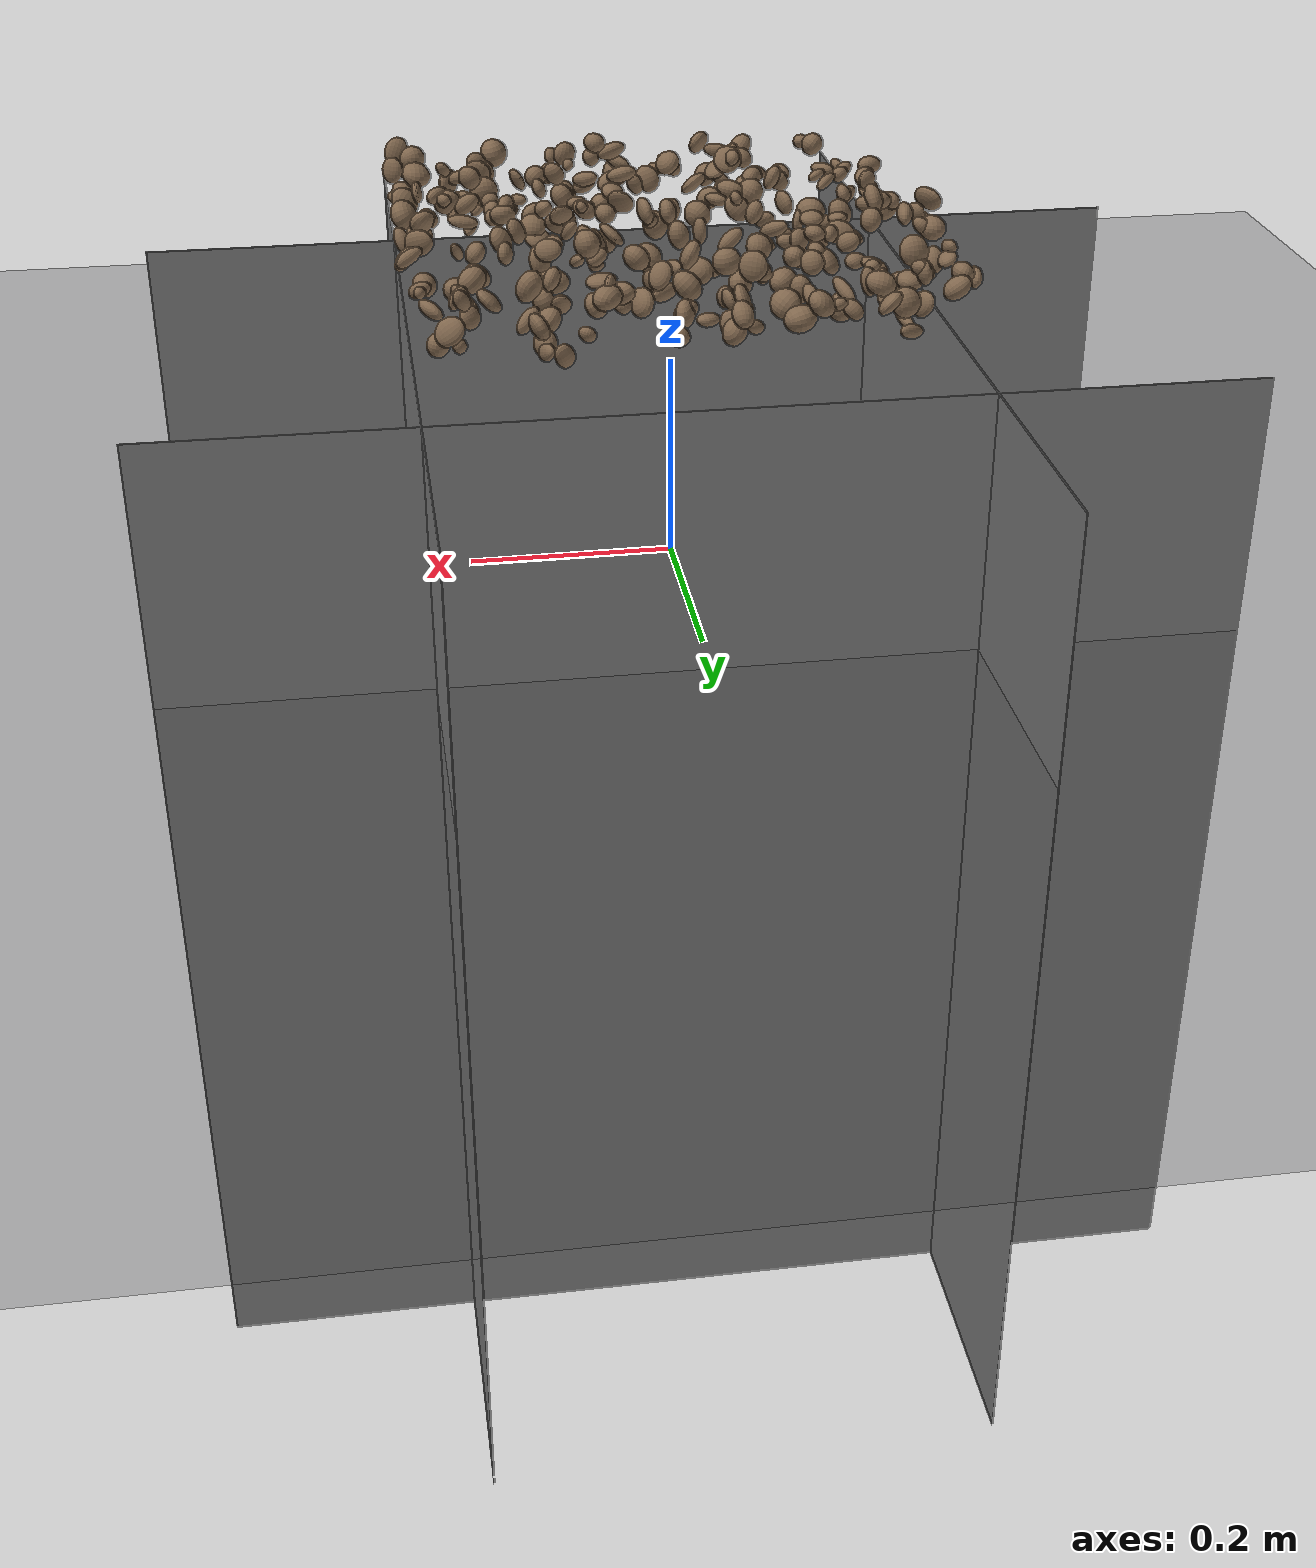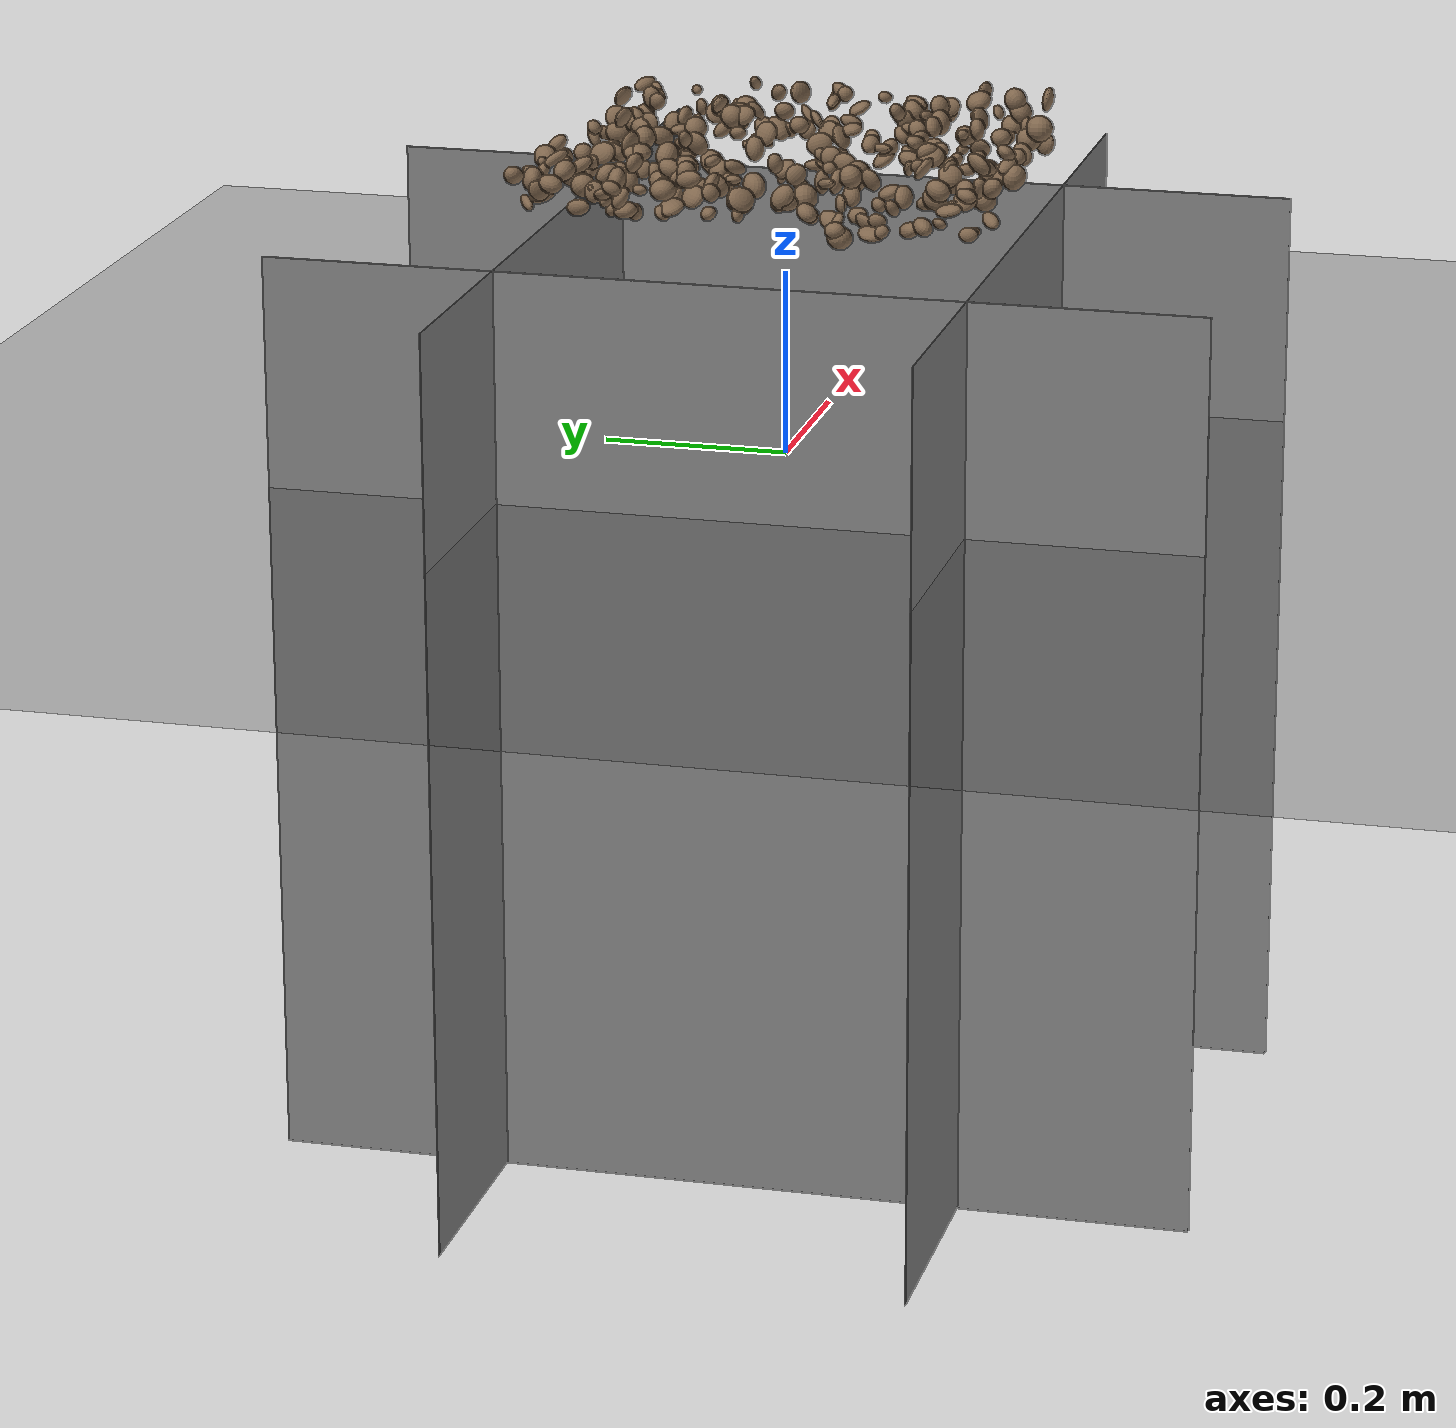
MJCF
<mujoco model="rocky_terrain_scene">

  <default>
    <default class="wall">
      <geom type="plane" size=".5 .5 .05" />
    </default>
  </default>

    <compiler angle="radian" inertiafromgeom="true" />
    <option timestep="0.002" gravity="0 0 -9.81" />

    <worldbody>

        <geom name="+x" class="wall" zaxis="1 0 0" pos="-.25 0 -.25" />
        <geom name="-x" class="wall" zaxis="-1 0 0" pos=".25 0 -.25" />
        <geom name="+y" class="wall" zaxis="0 1 0" pos="0 -.25 -.25" />
        <geom name="-y" class="wall" zaxis="0 -1 0" pos="0 .25 -.25" />

        <light name="sunlight" pos="5 5 5" dir="-1 -1 -1" diffuse="1 1 1" specular="0.5 0.5 0.5" ambient="0.5 0.5 0.5" />

        <geom name="ground_plane" type="plane" size="50 50 0.1" rgba="0.3 0.3 0.3 1" />

        <body name="rocky_terrain_body">

        </body>
    <body name="rock1" pos="-0.19893494325743716 -0.05025536319305107 0.3279177794750775"><joint type="free" /><geom type="ellipsoid" size="0.009794666094291228 0.008063589481748009 0.012479821381131446" quat="0.2933770791798721 0.40957105375614805 0.08158828609377874 0.21546358097020105" rgba="0.5 0.4 0.3 1" /><inertial pos="-0.19893494325743716 -0.05025536319305107 0.3279177794750775" quat="0.2933770791798721 0.40957105375614805 0.08158828609377874 0.21546358097020105" mass="8.698357740923812e-05" /></body><body name="rock2" pos="-0.09613453876190453 -0.04047330879119393 0.3204962367937986"><joint type="free" /><geom type="ellipsoid" size="0.006734666875923597 0.010678115712007934 0.008911600141473268" quat="0.43411550965568974 0.0230417757564103 0.25852981520113744 0.2843128993867626" rgba="0.5 0.4 0.3 1" /><inertial pos="-0.09613453876190453 -0.04047330879119393 0.3204962367937986" quat="0.43411550965568974 0.0230417757564103 0.25852981520113744 0.2843128993867626" mass="3.9323138524020545e-05" /></body><body name="rock3" pos="-0.01494975247563507 -0.19922593720878834 0.327029459988941"><joint type="free" /><geom type="ellipsoid" size="0.010190285356070217 0.006684218392850707 0.006125470081264342" quat="0.14274400503408674 0.23452067738037563 0.35866401885991867 0.26407129872561885" rgba="0.5 0.4 0.3 1" /><inertial pos="-0.01494975247563507 -0.19922593720878834 0.327029459988941" quat="0.14274400503408674 0.23452067738037563 0.35866401885991867 0.26407129872561885" mass="1.1877291045755743e-05" /></body><body name="rock4" pos="0.12669350270769153 0.2462591008655074 0.30393527237505824"><joint type="free" /><geom type="ellipsoid" size="0.006441817031002965 0.01302465107041327 0.008861363777752089" quat="0.1949013499878247 0.20697938586655493 0.4043430128829851 0.19377625126263526" rgba="0.5 0.4 0.3 1" /><inertial pos="0.12669350270769153 0.2462591008655074 0.30393527237505824" quat="0.1949013499878247 0.20697938586655493 0.4043430128829851 0.19377625126263526" mass="2.4946473005436022e-05" /></body><body name="rock5" pos="0.07905712179085511 0.1709583088265874 0.33337577583864325"><joint type="free" /><geom type="ellipsoid" size="0.010960172606603084 0.013676513366160378 0.005135921583983499" quat="0.26672095735452067 0.3186655298868615 0.1551954110830759 0.2594181016755419" rgba="0.5 0.4 0.3 1" /><inertial pos="0.07905712179085511 0.1709583088265874 0.33337577583864325" quat="0.26672095735452067 0.3186655298868615 0.1551954110830759 0.2594181016755419" mass="3.064949593439074e-05" /></body><body name="rock6" pos="0.12350979123031502 0.19398916797289462 0.3300841549060111"><joint type="free" /><geom type="ellipsoid" size="0.005477988412086193 0.012739735468770181 0.008749350242735128" quat="0.30926197638324077 0.1847863244906572 0.3624077149692068 0.1435439841568951" rgba="0.5 0.4 0.3 1" /><inertial pos="0.12350979123031502 0.19398916797289462 0.3300841549060111" quat="0.30926197638324077 0.1847863244906572 0.3624077149692068 0.1435439841568951" mass="3.559665047896268e-05" /></body><body name="rock7" pos="0.073863889204269 0.040278270831941965 0.3313487305319815"><joint type="free" /><geom type="ellipsoid" size="0.007009337856244279 0.013916865862378572 0.01233594208423866" quat="5.7833598217599114e-05 0.14168028113625625 0.36704600713781455 0.4912158781277116" rgba="0.5 0.4 0.3 1" /><inertial pos="0.073863889204269 0.040278270831941965 0.3313487305319815" quat="5.7833598217599114e-05 0.14168028113625625 0.36704600713781455 0.4912158781277116" mass="3.655972519511244e-05" /></body><body name="rock8" pos="0.045493766148333004 -0.2410314606984737 0.3293579014837154"><joint type="free" /><geom type="ellipsoid" size="0.007864488223148586 0.009277273496697578 0.008353010080814191" quat="0.2698344067999929 0.3260806850545474 0.2894869117071529 0.11459799643830677" rgba="0.5 0.4 0.3 1" /><inertial pos="0.045493766148333004 -0.2410314606984737 0.3293579014837154" quat="0.2698344067999929 0.3260806850545474 0.2894869117071529 0.11459799643830677" mass="6.67317996304894e-05" /></body><body name="rock9" pos="0.09311700195404143 0.04874438167227485 0.31883008899380966"><joint type="free" /><geom type="ellipsoid" size="0.013303135800658037 0.006167856961713951 0.00544040328713648" quat="0.32675429992537236 0.18118809843597505 0.019144023598954212 0.47291357803969836" rgba="0.5 0.4 0.3 1" /><inertial pos="0.09311700195404143 0.04874438167227485 0.31883008899380966" quat="0.32675429992537236 0.18118809843597505 0.019144023598954212 0.47291357803969836" mass="7.390142212995231e-05" /></body><body name="rock10" pos="0.2349541957100746 0.21816489391436522 0.3397937802375125"><joint type="free" /><geom type="ellipsoid" size="0.013141905303541104 0.006408832752840205 0.007596660828374557" quat="0.2556338464375104 0.0027464527842353276 0.2436001387568733 0.49801956202138087" rgba="0.5 0.4 0.3 1" /><inertial pos="0.2349541957100746 0.21816489391436522 0.3397937802375125" quat="0.2556338464375104 0.0027464527842353276 0.2436001387568733 0.49801956202138087" mass="4.228396619140731e-05" /></body><body name="rock11" pos="0.22838858622860753 -0.20608206426716447 0.3344158108123986"><joint type="free" /><geom type="ellipsoid" size="0.011127078501396711 0.013775159148325465 0.013909558411480373" quat="0.39870355304530825 0.10844746925926092 0.28301001900503947 0.20983895869039135" rgba="0.5 0.4 0.3 1" /><inertial pos="0.22838858622860753 -0.20608206426716447 0.3344158108123986" quat="0.39870355304530825 0.10844746925926092 0.28301001900503947 0.20983895869039135" mass="9.108347567644738e-05" /></body><body name="rock12" pos="-0.07624813224074045 -0.07372760136785161 0.32200350160169844"><joint type="free" /><geom type="ellipsoid" size="0.0075575651639508985 0.011017751025554707 0.01423563210807183" quat="0.358717917647786 0.16740947004192414 0.11569236133167511 0.3581802509786148" rgba="0.5 0.4 0.3 1" /><inertial pos="-0.07624813224074045 -0.07372760136785161 0.32200350160169844" quat="0.358717917647786 0.16740947004192414 0.11569236133167511 0.3581802509786148" mass="9.237708840067495e-05" /></body><body name="rock13" pos="0.16325946123550922 -0.13085302053163617 0.332761653044361"><joint type="free" /><geom type="ellipsoid" size="0.01084026044975067 0.014009693751080143 0.0140865196635673" quat="0.24032220110429658 0.24593584461322937 0.29399134893937734 0.2197506053430968" rgba="0.5 0.4 0.3 1" /><inertial pos="0.16325946123550922 -0.13085302053163617 0.332761653044361" quat="0.24032220110429658 0.24593584461322937 0.29399134893937734 0.2197506053430968" mass="4.422648524409123e-05" /></body><body name="rock14" pos="-0.19934727019048704 0.12080055547333085 0.309873403628351"><joint type="free" /><geom type="ellipsoid" size="0.012558299449248696 0.008791494609701496 0.013197183651065154" quat="0.13352574585283428 0.0913897514586144 0.41025407851499984 0.3648304241735514" rgba="0.5 0.4 0.3 1" /><inertial pos="-0.19934727019048704 0.12080055547333085 0.309873403628351" quat="0.13352574585283428 0.0913897514586144 0.41025407851499984 0.3648304241735514" mass="2.2572533757630593e-05" /></body><body name="rock15" pos="0.18795200855116806 0.04301993714583757 0.308927951760504"><joint type="free" /><geom type="ellipsoid" size="0.007517319509799744 0.0075230983665118 0.009723638835476665" quat="0.20130972922177223 0.44284249305160306 0.35478139118723684 0.0010663865393878344" rgba="0.5 0.4 0.3 1" /><inertial pos="0.18795200855116806 0.04301993714583757 0.308927951760504" quat="0.20130972922177223 0.44284249305160306 0.35478139118723684 0.0010663865393878344" mass="4.3919785400541604e-05" /></body><body name="rock16" pos="0.20790182193946805 0.19696908789248208 0.3391250218886552"><joint type="free" /><geom type="ellipsoid" size="0.007504714205149354 0.011474504895642688 0.006103484074500819" quat="0.3912480722469959 0.305889448606649 0.2783915818016332 0.024470897344721763" rgba="0.5 0.4 0.3 1" /><inertial pos="0.20790182193946805 0.19696908789248208 0.3391250218886552" quat="0.3912480722469959 0.305889448606649 0.2783915818016332 0.024470897344721763" mass="5.0419991132644205e-05" /></body><body name="rock17" pos="-0.093299973217283 -0.09373881027007386 0.3125064719200331"><joint type="free" /><geom type="ellipsoid" size="0.009893153033765457 0.01282768713342598 0.008395465885534402" quat="0.2770858283684626 0.3008039747542542 0.28389487108346123 0.1382153257938221" rgba="0.5 0.4 0.3 1" /><inertial pos="-0.093299973217283 -0.09373881027007386 0.3125064719200331" quat="0.2770858283684626 0.3008039747542542 0.28389487108346123 0.1382153257938221" mass="1.4779713710838265e-05" /></body><body name="rock18" pos="0.19212494097260385 0.06097480170868358 0.3075715729290926"><joint type="free" /><geom type="ellipsoid" size="0.005715599507979183 0.0070225972462829404 0.0062364212703401" quat="0.5134940258265499 0.036134102956342826 0.04548284506221906 0.40488902615488825" rgba="0.5 0.4 0.3 1" /><inertial pos="0.19212494097260385 0.06097480170868358 0.3075715729290926" quat="0.5134940258265499 0.036134102956342826 0.04548284506221906 0.40488902615488825" mass="7.191061365356746e-05" /></body><body name="rock19" pos="0.2310771926929865 -0.025744090000830666 0.3268730411468311"><joint type="free" /><geom type="ellipsoid" size="0.012648048923784773 0.01299974143562585 0.006100952814316388" quat="0.17197192274622408 0.667337116918391 0.12846045963986874 0.03223050069551614" rgba="0.5 0.4 0.3 1" /><inertial pos="0.2310771926929865 -0.025744090000830666 0.3268730411468311" quat="0.17197192274622408 0.667337116918391 0.12846045963986874 0.03223050069551614" mass="7.591257034517295e-05" /></body><body name="rock20" pos="0.19687495348474798 0.11854138277506798 0.3039524047223512"><joint type="free" /><geom type="ellipsoid" size="0.00783435980919733 0.013235204585810588 0.007278084336742727" quat="0.010073052182342019 0.33953045282262595 0.22494162682058302 0.4254548681744491" rgba="0.5 0.4 0.3 1" /><inertial pos="0.19687495348474798 0.11854138277506798 0.3039524047223512" quat="0.010073052182342019 0.33953045282262595 0.22494162682058302 0.4254548681744491" mass="4.364999395794444e-05" /></body><body name="rock21" pos="-0.12010207344850954 0.07645314147315829 0.3433607919245454"><joint type="free" /><geom type="ellipsoid" size="0.010479328188345292 0.007666714258575631 0.009851316902301982" quat="0.2959262542964678 0.27605819305853596 0.16738361177690622 0.26063194086809005" rgba="0.5 0.4 0.3 1" /><inertial pos="-0.12010207344850954 0.07645314147315829 0.3433607919245454" quat="0.2959262542964678 0.27605819305853596 0.16738361177690622 0.26063194086809005" mass="6.599659448365388e-05" /></body><body name="rock22" pos="-0.19806110613211741 -0.13213774672609246 0.3119207197850815"><joint type="free" /><geom type="ellipsoid" size="0.012074467296309031 0.0104537920388892 0.006020231406907968" quat="0.31525548292470745 0.28565709958642677 0.03389586281594633 0.36519155467291936" rgba="0.5 0.4 0.3 1" /><inertial pos="-0.19806110613211741 -0.13213774672609246 0.3119207197850815" quat="0.31525548292470745 0.28565709958642677 0.03389586281594633 0.36519155467291936" mass="8.385847690739369e-05" /></body><body name="rock23" pos="0.09375339147126749 -0.13839852528281094 0.34452946096370857"><joint type="free" /><geom type="ellipsoid" size="0.01003921249224437 0.0076417017913615 0.011811301661643816" quat="0.1382557036671132 0.13853745198501127 0.0967173978638355 0.6264894464840401" rgba="0.5 0.4 0.3 1" /><inertial pos="0.09375339147126749 -0.13839852528281094 0.34452946096370857" quat="0.1382557036671132 0.13853745198501127 0.0967173978638355 0.6264894464840401" mass="2.9933657148728615e-05" /></body><body name="rock24" pos="-0.03794951883525244 0.22918182887717237 0.31427066655668406"><joint type="free" /><geom type="ellipsoid" size="0.011141764872171413 0.00624409866586857 0.005489387583914914" quat="0.2931875930890132 0.4273571565656913 0.09436033824499575 0.18509491210029966" rgba="0.5 0.4 0.3 1" /><inertial pos="-0.03794951883525244 0.22918182887717237 0.31427066655668406" quat="0.2931875930890132 0.4273571565656913 0.09436033824499575 0.18509491210029966" mass="5.94094598814109e-05" /></body><body name="rock25" pos="0.13506032355301262 0.15809414185992987 0.3218246560324434"><joint type="free" /><geom type="ellipsoid" size="0.011512501715289065 0.0095294364085868 0.01304271451117759" quat="0.3374461105662458 0.11543917763565016 0.0565719853680109 0.49054272643009317" rgba="0.5 0.4 0.3 1" /><inertial pos="0.13506032355301262 0.15809414185992987 0.3218246560324434" quat="0.3374461105662458 0.11543917763565016 0.0565719853680109 0.49054272643009317" mass="1.073128108483585e-05" /></body><body name="rock26" pos="-0.0025091886861288715 0.03299237263736737 0.3334582349362912"><joint type="free" /><geom type="ellipsoid" size="0.01010674997192324 0.013613683921351039 0.00979447272924916" quat="0.28804465651814076 0.3087910477465 0.23934183798971362 0.1638224577456457" rgba="0.5 0.4 0.3 1" /><inertial pos="-0.0025091886861288715 0.03299237263736737 0.3334582349362912" quat="0.28804465651814076 0.3087910477465 0.23934183798971362 0.1638224577456457" mass="9.486969873789428e-05" /></body><body name="rock27" pos="0.14061763982466358 0.22324178265072742 0.30711965528961593"><joint type="free" /><geom type="ellipsoid" size="0.01362878010681191 0.012466192479089595 0.010050691772281416" quat="0.21746768309660017 0.22922397780508474 0.2608691236034413 0.2924392154948738" rgba="0.5 0.4 0.3 1" /><inertial pos="0.14061763982466358 0.22324178265072742 0.30711965528961593" quat="0.21746768309660017 0.22922397780508474 0.2608691236034413 0.2924392154948738" mass="4.257954307358595e-05" /></body><body name="rock28" pos="0.14491970466210086 -0.10209644705893739 0.3285290751661306"><joint type="free" /><geom type="ellipsoid" size="0.012200529883293532 0.006939568992902899 0.0069867119055125465" quat="0.1898625983858111 0.4131201932206116 0.30462821859961126 0.09238898979396606" rgba="0.5 0.4 0.3 1" /><inertial pos="0.14491970466210086 -0.10209644705893739 0.3285290751661306" quat="0.1898625983858111 0.4131201932206116 0.30462821859961126 0.09238898979396606" mass="2.556826534211638e-05" /></body><body name="rock29" pos="0.05108936742330222 -0.03358249288855192 0.315405608328922"><joint type="free" /><geom type="ellipsoid" size="0.012673674921337426 0.005772624330103373 0.014711469548150707" quat="0.38427287930175186 0.29496590090633656 0.016599405652495444 0.3041618141394162" rgba="0.5 0.4 0.3 1" /><inertial pos="0.05108936742330222 -0.03358249288855192 0.315405608328922" quat="0.38427287930175186 0.29496590090633656 0.016599405652495444 0.3041618141394162" mass="6.648433301390754e-05" /></body><body name="rock30" pos="-0.04879164143306186 0.15713542004927605 0.3428757882438639"><joint type="free" /><geom type="ellipsoid" size="0.0063971897223899996 0.013821160195442446 0.012948361158107359" quat="0.2868251367401842 0.3048929240642426 0.16323547942927624 0.24504645976629702" rgba="0.5 0.4 0.3 1" /><inertial pos="-0.04879164143306186 0.15713542004927605 0.3428757882438639" quat="0.2868251367401842 0.3048929240642426 0.16323547942927624 0.24504645976629702" mass="5.986668299980278e-05" /></body><body name="rock31" pos="-0.09386184788616081 -0.22831669648092034 0.3281696162982567"><joint type="free" /><geom type="ellipsoid" size="0.00751740101918802 0.007645978420896973 0.01452723340659754" quat="0.00614840064825135 0.5280799179502109 0.271554799112655 0.19421688228888276" rgba="0.5 0.4 0.3 1" /><inertial pos="-0.09386184788616081 -0.22831669648092034 0.3281696162982567" quat="0.00614840064825135 0.5280799179502109 0.271554799112655 0.19421688228888276" mass="9.578572367888128e-05" /></body><body name="rock32" pos="-0.10962901692946958 -0.24580170309539612 0.3330024858640992"><joint type="free" /><geom type="ellipsoid" size="0.010177608159663974 0.01357723515335671 0.009873041226468905" quat="0.25452751217008784 0.14294762467176164 0.14624996072106525 0.45627490243708535" rgba="0.5 0.4 0.3 1" /><inertial pos="-0.10962901692946958 -0.24580170309539612 0.3330024858640992" quat="0.25452751217008784 0.14294762467176164 0.14624996072106525 0.45627490243708535" mass="4.151776797046685e-05" /></body><body name="rock33" pos="-0.13534561467705514 0.07387269963489274 0.3410858008563695"><joint type="free" /><geom type="ellipsoid" size="0.00953517576713988 0.007853178111966775 0.006036457475956542" quat="0.30444523502242876 0.33424877453462254 0.22321152390004959 0.13809446654289914" rgba="0.5 0.4 0.3 1" /><inertial pos="-0.13534561467705514 0.07387269963489274 0.3410858008563695" quat="0.30444523502242876 0.33424877453462254 0.22321152390004959 0.13809446654289914" mass="9.572722557087218e-05" /></body><body name="rock34" pos="-0.03855296347204756 0.09985686979989694 0.3483653635712279"><joint type="free" /><geom type="ellipsoid" size="0.0065313019917069975 0.0073253619114936495 0.01383822540776107" quat="0.06837931552953205 0.47790492888889113 0.22248935199601746 0.2312264035855593" rgba="0.5 0.4 0.3 1" /><inertial pos="-0.03855296347204756 0.09985686979989694 0.3483653635712279" quat="0.06837931552953205 0.47790492888889113 0.22248935199601746 0.2312264035855593" mass="8.703719591985288e-05" /></body><body name="rock35" pos="0.24008410741334846 -0.12509308080965936 0.3277136571568874"><joint type="free" /><geom type="ellipsoid" size="0.009000537520449327 0.014640206558438281 0.012422611363563794" quat="0.03310855715903026 0.30407382350361245 0.41361711358798503 0.24920050574937225" rgba="0.5 0.4 0.3 1" /><inertial pos="0.24008410741334846 -0.12509308080965936 0.3277136571568874" quat="0.03310855715903026 0.30407382350361245 0.41361711358798503 0.24920050574937225" mass="2.7375131645770058e-05" /></body><body name="rock36" pos="0.2303240148400092 0.21621716050874185 0.30813502774913704"><joint type="free" /><geom type="ellipsoid" size="0.010548967665280743 0.011129469813463293 0.009935810046135748" quat="0.44711611203517543 0.14257963002925272 0.3283843493905232 0.08191990854504859" rgba="0.5 0.4 0.3 1" /><inertial pos="0.2303240148400092 0.21621716050874185 0.30813502774913704" quat="0.44711611203517543 0.14257963002925272 0.3283843493905232 0.08191990854504859" mass="3.1477074985003535e-05" /></body><body name="rock37" pos="-0.018602427908191332 0.23896469779151075 0.3147738630916886"><joint type="free" /><geom type="ellipsoid" size="0.011083906046821027 0.012715347771534338 0.009902927471788957" quat="0.21339059967046994 0.1022513357007334 0.23447985852293748 0.4498782061058591" rgba="0.5 0.4 0.3 1" /><inertial pos="-0.018602427908191332 0.23896469779151075 0.3147738630916886" quat="0.21339059967046994 0.1022513357007334 0.23447985852293748 0.4498782061058591" mass="9.001321223251494e-05" /></body><body name="rock38" pos="0.1457546244869924 0.22588482581877067 0.322891156949073"><joint type="free" /><geom type="ellipsoid" size="0.01252028567054636 0.012903767776037165 0.006991379615926496" quat="0.11360715764179079 0.33476431890991754 0.28164350719139 0.2699850162569017" rgba="0.5 0.4 0.3 1" /><inertial pos="0.1457546244869924 0.22588482581877067 0.322891156949073" quat="0.11360715764179079 0.33476431890991754 0.28164350719139 0.2699850162569017" mass="8.799465817167849e-05" /></body><body name="rock39" pos="0.08764007559738807 0.08036749144907862 0.34489205377155746"><joint type="free" /><geom type="ellipsoid" size="0.012719013583794455 0.013470226523595766 0.011714434337128677" quat="0.3366044170254788 0.10609262010151348 0.38172724102099315 0.1755757218520146" rgba="0.5 0.4 0.3 1" /><inertial pos="0.08764007559738807 0.08036749144907862 0.34489205377155746" quat="0.3366044170254788 0.10609262010151348 0.38172724102099315 0.1755757218520146" mass="2.1282165807157308e-05" /></body><body name="rock40" pos="-0.13319604102072002 0.03971993475292296 0.32410530257858583"><joint type="free" /><geom type="ellipsoid" size="0.011423493439154973 0.008697663422151388 0.013778273020705358" quat="0.13566509987062023 0.4492924395454642 0.38693863801138595 0.028103822572529576" rgba="0.5 0.4 0.3 1" /><inertial pos="-0.13319604102072002 0.03971993475292296 0.32410530257858583" quat="0.13566509987062023 0.4492924395454642 0.38693863801138595 0.028103822572529576" mass="3.867005957847649e-05" /></body><body name="rock41" pos="-0.1510310935809513 0.04233891450494115 0.3316659506846131"><joint type="free" /><geom type="ellipsoid" size="0.00642321240474898 0.011429538053588867 0.01447623794822753" quat="0.19854605413354612 0.2829112785214706 0.16989998524518976 0.34864268209979354" rgba="0.5 0.4 0.3 1" /><inertial pos="-0.1510310935809513 0.04233891450494115 0.3316659506846131" quat="0.19854605413354612 0.2829112785214706 0.16989998524518976 0.34864268209979354" mass="3.0996538826081477e-05" /></body><body name="rock42" pos="-0.038969034479753084 -0.08369006417739139 0.3149865270679944"><joint type="free" /><geom type="ellipsoid" size="0.013568158105692292 0.013642261242320226 0.01212920470445913" quat="0.17209871479973973 0.08917613617274894 0.454014090114791 0.28471105891272025" rgba="0.5 0.4 0.3 1" /><inertial pos="-0.038969034479753084 -0.08369006417739139 0.3149865270679944" quat="0.17209871479973973 0.08917613617274894 0.454014090114791 0.28471105891272025" mass="4.295409190808621e-05" /></body><body name="rock43" pos="0.08221480215593868 0.17967049444921446 0.3292040620005424"><joint type="free" /><geom type="ellipsoid" size="0.014742971039634883 0.010637612016828064 0.011591601164787906" quat="0.3866006971822685 0.31962011514690053 0.16666349539285275 0.1271156922779782" rgba="0.5 0.4 0.3 1" /><inertial pos="0.08221480215593868 0.17967049444921446 0.3292040620005424" quat="0.3866006971822685 0.31962011514690053 0.16666349539285275 0.1271156922779782" mass="5.3982473387548486e-05" /></body><body name="rock44" pos="0.021164732046864365 0.10706066597006098 0.305610519088798"><joint type="free" /><geom type="ellipsoid" size="0.014731959194740837 0.008376893309385132 0.005676193892738486" quat="0.42783665809556565 0.3480173710572901 0.12219097651714735 0.101954994329997" rgba="0.5 0.4 0.3 1" /><inertial pos="0.021164732046864365 0.10706066597006098 0.305610519088798" quat="0.42783665809556565 0.3480173710572901 0.12219097651714735 0.101954994329997" mass="4.575424942355488e-05" /></body><body name="rock45" pos="-0.2037361203715236 0.15266928651074696 0.32807019137898585"><joint type="free" /><geom type="ellipsoid" size="0.010528333564813124 0.011851892885643693 0.0069439679277404145" quat="0.2066662048390407 0.27447823611232386 0.26076020021478924 0.2580953588338461" rgba="0.5 0.4 0.3 1" /><inertial pos="-0.2037361203715236 0.15266928651074696 0.32807019137898585" quat="0.2066662048390407 0.27447823611232386 0.26076020021478924 0.2580953588338461" mass="8.719819471168642e-05" /></body><body name="rock46" pos="0.036345996730844266 -0.17603150558112296 0.32386562288994736"><joint type="free" /><geom type="ellipsoid" size="0.006604982825036808 0.00845624731795324 0.01218426144149303" quat="0.046953557262434706 0.44802717600474157 0.24098044085731654 0.2640388258755072" rgba="0.5 0.4 0.3 1" /><inertial pos="0.036345996730844266 -0.17603150558112296 0.32386562288994736" quat="0.046953557262434706 0.44802717600474157 0.24098044085731654 0.2640388258755072" mass="4.723013958926915e-05" /></body><body name="rock47" pos="0.21037262106047872 -0.09379830400320094 0.34150233783600575"><joint type="free" /><geom type="ellipsoid" size="0.014444606351537648 0.008785945834835544 0.007163827468264199" quat="0.4220807861059162 0.2403961089773946 0.10611854685963018 0.23140455805705903" rgba="0.5 0.4 0.3 1" /><inertial pos="0.21037262106047872 -0.09379830400320094 0.34150233783600575" quat="0.4220807861059162 0.2403961089773946 0.10611854685963018 0.23140455805705903" mass="1.7179198684572524e-05" /></body><body name="rock48" pos="0.06401343040462532 0.140972345303217 0.308191948269262"><joint type="free" /><geom type="ellipsoid" size="0.008825779871340866 0.006973753911264428 0.009604639355640826" quat="0.33811641242063817 0.003007648355510596 0.3360126262222368 0.3228633130016144" rgba="0.5 0.4 0.3 1" /><inertial pos="0.06401343040462532 0.140972345303217 0.308191948269262" quat="0.33811641242063817 0.003007648355510596 0.3360126262222368 0.3228633130016144" mass="7.573317546668975e-05" /></body><body name="rock49" pos="-0.02450533665626886 0.2439540939816709 0.3311686674806632"><joint type="free" /><geom type="ellipsoid" size="0.009686461686987677 0.00786868158449715 0.012649318387616439" quat="0.6725050851318578 0.27640041744321825 0.012791471177574076 0.03830302624734993" rgba="0.5 0.4 0.3 1" /><inertial pos="-0.02450533665626886 0.2439540939816709 0.3311686674806632" quat="0.6725050851318578 0.27640041744321825 0.012791471177574076 0.03830302624734993" mass="6.0473972778056785e-05" /></body><body name="rock50" pos="-0.21982617576794028 -0.10709147610316566 0.31729469532417964"><joint type="free" /><geom type="ellipsoid" size="0.010429114252001628 0.005532412717180374 0.010328425731246817" quat="0.5285826720868487 0.18078447334831646 0.11127881347191677 0.179354041092918" rgba="0.5 0.4 0.3 1" /><inertial pos="-0.21982617576794028 -0.10709147610316566 0.31729469532417964" quat="0.5285826720868487 0.18078447334831646 0.11127881347191677 0.179354041092918" mass="5.472279281384634e-05" /></body><body name="rock51" pos="-0.09320647197593013 0.23702913275808468 0.33429267957946496"><joint type="free" /><geom type="ellipsoid" size="0.01223163089673509 0.009872408469673917 0.014231841101711797" quat="0.3518372394671961 0.010742268394529035 0.2882235462998858 0.34919694583838917" rgba="0.5 0.4 0.3 1" /><inertial pos="-0.09320647197593013 0.23702913275808468 0.33429267957946496" quat="0.3518372394671961 0.010742268394529035 0.2882235462998858 0.34919694583838917" mass="2.9231632260200404e-05" /></body><body name="rock52" pos="-0.20314774277574082 -0.04685965661385616 0.3347003169446122"><joint type="free" /><geom type="ellipsoid" size="0.014441893907903548 0.01073720401177617 0.008312631765380583" quat="0.32919076907537514 0.1679726396345822 0.41624526403427065 0.086591327255772" rgba="0.5 0.4 0.3 1" /><inertial pos="-0.20314774277574082 -0.04685965661385616 0.3347003169446122" quat="0.32919076907537514 0.1679726396345822 0.41624526403427065 0.086591327255772" mass="3.1851660664895625e-05" /></body><body name="rock53" pos="0.2264781095906202 -0.1597104890560722 0.34308138031997276"><joint type="free" /><geom type="ellipsoid" size="0.010585236592415784 0.014184497620911573 0.014105563550509535" quat="0.04615946487994029 0.3580854330673775 0.12884034315421342 0.46691475889846884" rgba="0.5 0.4 0.3 1" /><inertial pos="0.2264781095906202 -0.1597104890560722 0.34308138031997276" quat="0.04615946487994029 0.3580854330673775 0.12884034315421342 0.46691475889846884" mass="9.259196966272736e-05" /></body><body name="rock54" pos="0.061000940507227486 0.00025894986842289747 0.3462117180042534"><joint type="free" /><geom type="ellipsoid" size="0.010490734273141046 0.009293725587001127 0.009468732935349665" quat="0.23829515020165487 0.1534546502451676 0.2671217220960708 0.34112847745710667" rgba="0.5 0.4 0.3 1" /><inertial pos="0.061000940507227486 0.00025894986842289747 0.3462117180042534" quat="0.23829515020165487 0.1534546502451676 0.2671217220960708 0.34112847745710667" mass="3.845916432508823e-05" /></body><body name="rock55" pos="0.10910037816039175 -0.1705587159365276 0.33302382660312485"><joint type="free" /><geom type="ellipsoid" size="0.011303822641243544 0.010897905812337174 0.010323999441525507" quat="0.3679550694169389 0.2642596410635992 0.018730436629214045 0.34905485289024785" rgba="0.5 0.4 0.3 1" /><inertial pos="0.10910037816039175 -0.1705587159365276 0.33302382660312485" quat="0.3679550694169389 0.2642596410635992 0.018730436629214045 0.34905485289024785" mass="6.638688540413187e-05" /></body><body name="rock56" pos="0.021338282596905844 0.006321330184372365 0.30735261627699273"><joint type="free" /><geom type="ellipsoid" size="0.012417168695223857 0.012734286461070565 0.007519139729100311" quat="0.20082286759015505 0.4961356047242404 0.2931451061753315 0.009896421510273116" rgba="0.5 0.4 0.3 1" /><inertial pos="0.021338282596905844 0.006321330184372365 0.30735261627699273" quat="0.20082286759015505 0.4961356047242404 0.2931451061753315 0.009896421510273116" mass="4.383270707535094e-05" /></body><body name="rock57" pos="-0.22692878685582696 -0.18506186982102768 0.3142840180611096"><joint type="free" /><geom type="ellipsoid" size="0.009179622107373947 0.008019807485069646 0.012753933517695902" quat="0.2196700828154623 0.022070171192084962 0.4604925480777614 0.29776719791469125" rgba="0.5 0.4 0.3 1" /><inertial pos="-0.22692878685582696 -0.18506186982102768 0.3142840180611096" quat="0.2196700828154623 0.022070171192084962 0.4604925480777614 0.29776719791469125" mass="5.03636238760285e-05" /></body><body name="rock58" pos="0.17704954804210188 -0.12715542915601924 0.347290404630231"><joint type="free" /><geom type="ellipsoid" size="0.01106993260953099 0.01181752543816582 0.008673492489433741" quat="0.09598587696419508 0.13051055235328604 0.43208494419766336 0.3414186264848555" rgba="0.5 0.4 0.3 1" /><inertial pos="0.17704954804210188 -0.12715542915601924 0.347290404630231" quat="0.09598587696419508 0.13051055235328604 0.43208494419766336 0.3414186264848555" mass="1.0413207727129316e-05" /></body><body name="rock59" pos="0.08689062008499321 0.06795772764514746 0.3468526555705004"><joint type="free" /><geom type="ellipsoid" size="0.012207779166898598 0.011146919841142598 0.0074194499209869515" quat="0.22519077202313748 0.28167834880333703 0.36767321786481993 0.12545766130870556" rgba="0.5 0.4 0.3 1" /><inertial pos="0.08689062008499321 0.06795772764514746 0.3468526555705004" quat="0.22519077202313748 0.28167834880333703 0.36767321786481993 0.12545766130870556" mass="1.567338399686547e-05" /></body><body name="rock60" pos="-0.010558479038143442 -0.06679286789823524 0.32438922846703355"><joint type="free" /><geom type="ellipsoid" size="0.01361971968274285 0.01245299248473836 0.008741676035896153" quat="0.2523922847482351 0.2753784034158601 0.18339117013884318 0.2888381416970615" rgba="0.5 0.4 0.3 1" /><inertial pos="-0.010558479038143442 -0.06679286789823524 0.32438922846703355" quat="0.2523922847482351 0.2753784034158601 0.18339117013884318 0.2888381416970615" mass="7.851978383468075e-05" /></body><body name="rock61" pos="0.10033176973999447 -0.21745554167502318 0.3176363908032611"><joint type="free" /><geom type="ellipsoid" size="0.006427593954040891 0.007035718691484333 0.006059839542927025" quat="0.13476392331472148 0.34879224831497235 0.02408233993736153 0.49236148843294464" rgba="0.5 0.4 0.3 1" /><inertial pos="0.10033176973999447 -0.21745554167502318 0.3176363908032611" quat="0.13476392331472148 0.34879224831497235 0.02408233993736153 0.49236148843294464" mass="2.3841266274105945e-05" /></body><body name="rock62" pos="-0.18671241335504307 0.2168704520959543 0.32198454386443603"><joint type="free" /><geom type="ellipsoid" size="0.012910129549919516 0.010953177242483302 0.005662274905141388" quat="0.04327748245886607 0.2811828695110061 0.22722897357465527 0.4483106744554727" rgba="0.5 0.4 0.3 1" /><inertial pos="-0.18671241335504307 0.2168704520959543 0.32198454386443603" quat="0.04327748245886607 0.2811828695110061 0.22722897357465527 0.4483106744554727" mass="5.286366216975399e-05" /></body><body name="rock63" pos="-0.11650155028791387 -0.021592583944830046 0.30421114016329304"><joint type="free" /><geom type="ellipsoid" size="0.008673614458712566 0.007764214326687131 0.01213415735710336" quat="0.1863861314489626 0.2781485369442425 0.1949007403876892 0.3405645912191056" rgba="0.5 0.4 0.3 1" /><inertial pos="-0.11650155028791387 -0.021592583944830046 0.30421114016329304" quat="0.1863861314489626 0.2781485369442425 0.1949007403876892 0.3405645912191056" mass="6.650334139744746e-05" /></body><body name="rock64" pos="-0.22125365347923448 0.11977066147866161 0.32775335875368233"><joint type="free" /><geom type="ellipsoid" size="0.012647291877089677 0.007157848480344448 0.009173889687488753" quat="0.3912988916031502 0.056154185785281995 0.3747879959025058 0.17775892670906218" rgba="0.5 0.4 0.3 1" /><inertial pos="-0.22125365347923448 0.11977066147866161 0.32775335875368233" quat="0.3912988916031502 0.056154185785281995 0.3747879959025058 0.17775892670906218" mass="5.464411543660314e-05" /></body><body name="rock65" pos="-0.16784784492574223 0.22965773741601775 0.329085225928989"><joint type="free" /><geom type="ellipsoid" size="0.009814830985152309 0.013271904777338181 0.014153163742661519" quat="0.1496939405197887 0.24684998846448616 0.2743860391826426 0.3290700318330825" rgba="0.5 0.4 0.3 1" /><inertial pos="-0.16784784492574223 0.22965773741601775 0.329085225928989" quat="0.1496939405197887 0.24684998846448616 0.2743860391826426 0.3290700318330825" mass="2.7554333058722895e-05" /></body><body name="rock66" pos="0.07189870165108736 -0.07534495971368871 0.32722285371405097"><joint type="free" /><geom type="ellipsoid" size="0.009279216177676554 0.008769133306517327 0.011903401269552503" quat="0.24538487504726328 0.26454261058563827 0.09122778750419372 0.3988447268629047" rgba="0.5 0.4 0.3 1" /><inertial pos="0.07189870165108736 -0.07534495971368871 0.32722285371405097" quat="0.24538487504726328 0.26454261058563827 0.09122778750419372 0.3988447268629047" mass="1.2629418158785546e-05" /></body><body name="rock67" pos="-0.09658886876371758 0.10036490621677863 0.3304462235658632"><joint type="free" /><geom type="ellipsoid" size="0.010000461745299425 0.013310998303766773 0.009874371841823668" quat="0.49666974105506784 0.10607564893528819 0.34429964790822404 0.05295496210142" rgba="0.5 0.4 0.3 1" /><inertial pos="-0.09658886876371758 0.10036490621677863 0.3304462235658632" quat="0.49666974105506784 0.10607564893528819 0.34429964790822404 0.05295496210142" mass="8.416478512395974e-05" /></body><body name="rock68" pos="0.18565876220229283 -0.11099284036578305 0.3346538672155146"><joint type="free" /><geom type="ellipsoid" size="0.005326838548914691 0.005098729446047235 0.0106677673083716" quat="0.21732183109704345 0.4010411421444674 0.08917956138549235 0.29245746537299677" rgba="0.5 0.4 0.3 1" /><inertial pos="0.18565876220229283 -0.11099284036578305 0.3346538672155146" quat="0.21732183109704345 0.4010411421444674 0.08917956138549235 0.29245746537299677" mass="7.43274291581018e-05" /></body><body name="rock69" pos="0.14133211436490362 0.2389682642404647 0.3052516309108506"><joint type="free" /><geom type="ellipsoid" size="0.005051979749244379 0.0077724507140665075 0.013501950769917566" quat="0.352217007696907 0.5044011470509393 0.04752178490504145 0.09586006034711228" rgba="0.5 0.4 0.3 1" /><inertial pos="0.14133211436490362 0.2389682642404647 0.3052516309108506" quat="0.352217007696907 0.5044011470509393 0.04752178490504145 0.09586006034711228" mass="6.651204492272383e-05" /></body><body name="rock70" pos="-0.05561175905664123 -0.21298780815063745 0.30655709270749726"><joint type="free" /><geom type="ellipsoid" size="0.014040410707924687 0.01456899777131394 0.006507163290806807" quat="0.40013330532494146 0.2048834359634881 0.05021243191133384 0.3447708268002366" rgba="0.5 0.4 0.3 1" /><inertial pos="-0.05561175905664123 -0.21298780815063745 0.30655709270749726" quat="0.40013330532494146 0.2048834359634881 0.05021243191133384 0.3447708268002366" mass="5.07720791883808e-05" /></body><body name="rock71" pos="-0.21028233380802874 0.1386427506914441 0.32114513814655155"><joint type="free" /><geom type="ellipsoid" size="0.005290029704487286 0.007534377694918049 0.0065513148107821184" quat="0.017024689852631007 0.5285631507318115 0.30346308617112017 0.15094907324443735" rgba="0.5 0.4 0.3 1" /><inertial pos="-0.21028233380802874 0.1386427506914441 0.32114513814655155" quat="0.017024689852631007 0.5285631507318115 0.30346308617112017 0.15094907324443735" mass="9.504547924832383e-05" /></body><body name="rock72" pos="-0.08196640711376774 -0.21163530779907175 0.31168612283749975"><joint type="free" /><geom type="ellipsoid" size="0.012003364676904861 0.006313356012425098 0.014305853931350903" quat="0.3310795460905087 0.24706972686220643 0.06340629250450801 0.35844443454277675" rgba="0.5 0.4 0.3 1" /><inertial pos="-0.08196640711376774 -0.21163530779907175 0.31168612283749975" quat="0.3310795460905087 0.24706972686220643 0.06340629250450801 0.35844443454277675" mass="2.3809138199972196e-05" /></body><body name="rock73" pos="-0.09217668863232292 -0.02901760262288361 0.3016533940263591"><joint type="free" /><geom type="ellipsoid" size="0.005274867449892575 0.009344738338722316 0.013775130293191554" quat="0.37916350282361616 0.25241956924278275 0.19143823223190423 0.17697869570169686" rgba="0.5 0.4 0.3 1" /><inertial pos="-0.09217668863232292 -0.02901760262288361 0.3016533940263591" quat="0.37916350282361616 0.25241956924278275 0.19143823223190423 0.17697869570169686" mass="9.130353200538434e-05" /></body><body name="rock74" pos="-0.07252945262607974 -0.0945272026060735 0.33421174988886837"><joint type="free" /><geom type="ellipsoid" size="0.010787133724945514 0.009333917101768213 0.013807975812824665" quat="0.26426202341370686 0.31675463714772234 0.11806477554315777 0.300918563895413" rgba="0.5 0.4 0.3 1" /><inertial pos="-0.07252945262607974 -0.0945272026060735 0.33421174988886837" quat="0.26426202341370686 0.31675463714772234 0.11806477554315777 0.300918563895413" mass="7.286546362171909e-05" /></body><body name="rock75" pos="0.08189874372279993 0.13557274389776308 0.32880454847129403"><joint type="free" /><geom type="ellipsoid" size="0.011891886267887267 0.0062831310649558115 0.013894016264300379" quat="0.2561269843301005 0.2491095103177193 0.27523701140441337 0.21952649394776685" rgba="0.5 0.4 0.3 1" /><inertial pos="0.08189874372279993 0.13557274389776308 0.32880454847129403" quat="0.2561269843301005 0.2491095103177193 0.27523701140441337 0.21952649394776685" mass="1.280400371515198e-05" /></body><body name="rock76" pos="-0.08430207513466315 0.11427706260516185 0.3137716596743368"><joint type="free" /><geom type="ellipsoid" size="0.011650211606622864 0.011106067049394572 0.014209884510804599" quat="0.11034234386904275 0.1666736261659715 0.39090229734594895 0.3320817326190368" rgba="0.5 0.4 0.3 1" /><inertial pos="-0.08430207513466315 0.11427706260516185 0.3137716596743368" quat="0.11034234386904275 0.1666736261659715 0.39090229734594895 0.3320817326190368" mass="5.57142090334178e-05" /></body><body name="rock77" pos="0.14968476116259 0.18640825253053733 0.3447634198558669"><joint type="free" /><geom type="ellipsoid" size="0.010974550368469376 0.014994136571967107 0.010175674596732343" quat="0.4440891025404786 0.3403842762130827 0.029913195073379743 0.18561342617305884" rgba="0.5 0.4 0.3 1" /><inertial pos="0.14968476116259 0.18640825253053733 0.3447634198558669" quat="0.4440891025404786 0.3403842762130827 0.029913195073379743 0.18561342617305884" mass="8.920583075354741e-05" /></body><body name="rock78" pos="-0.23607165727242085 -0.10940900130968667 0.3117704348603222"><joint type="free" /><geom type="ellipsoid" size="0.010985299411165791 0.008459464459957194 0.009906144346378029" quat="0.31491372296651454 0.22235950929758475 0.21671981609480653 0.24600695164109407" rgba="0.5 0.4 0.3 1" /><inertial pos="-0.23607165727242085 -0.10940900130968667 0.3117704348603222" quat="0.31491372296651454 0.22235950929758475 0.21671981609480653 0.24600695164109407" mass="8.630423599310789e-05" /></body><body name="rock79" pos="-0.15406578780906222 0.017231427459480697 0.3375302931797971"><joint type="free" /><geom type="ellipsoid" size="0.008858671842129823 0.005047137685543316 0.008675482969891573" quat="0.04621940008915533 0.09519905285582571 0.42612420394626893 0.43245734310875006" rgba="0.5 0.4 0.3 1" /><inertial pos="-0.15406578780906222 0.017231427459480697 0.3375302931797971" quat="0.04621940008915533 0.09519905285582571 0.42612420394626893 0.43245734310875006" mass="3.5824974573617135e-05" /></body><body name="rock80" pos="-0.2354960429367654 -0.20098769568075892 0.3208264066033603"><joint type="free" /><geom type="ellipsoid" size="0.013998328407867765 0.00911959280397389 0.009738454492868231" quat="0.26895238685062134 0.49495554055129937 0.1217278160868677 0.1143642565112116" rgba="0.5 0.4 0.3 1" /><inertial pos="-0.2354960429367654 -0.20098769568075892 0.3208264066033603" quat="0.26895238685062134 0.49495554055129937 0.1217278160868677 0.1143642565112116" mass="2.7919035371285506e-05" /></body><body name="rock81" pos="0.06746092048606478 0.1541637438091608 0.32371119463366704"><joint type="free" /><geom type="ellipsoid" size="0.014931102237603917 0.009138912351815357 0.010236009149200918" quat="0.23926161998743706 0.13125519377965345 0.030421198475122126 0.5990619877577873" rgba="0.5 0.4 0.3 1" /><inertial pos="0.06746092048606478 0.1541637438091608 0.32371119463366704" quat="0.23926161998743706 0.13125519377965345 0.030421198475122126 0.5990619877577873" mass="5.1383714548662555e-05" /></body><body name="rock82" pos="-0.23003287162234715 0.07237418270482027 0.34169208816972807"><joint type="free" /><geom type="ellipsoid" size="0.013558766737843366 0.01123995397613564 0.012945928912615375" quat="0.26297906053106096 0.2050490906409653 0.2680651442520197 0.263906704575954" rgba="0.5 0.4 0.3 1" /><inertial pos="-0.23003287162234715 0.07237418270482027 0.34169208816972807" quat="0.26297906053106096 0.2050490906409653 0.2680651442520197 0.263906704575954" mass="2.4424224437800906e-05" /></body><body name="rock83" pos="0.18427793817043098 0.05369458048470782 0.31099749177402697"><joint type="free" /><geom type="ellipsoid" size="0.012009641476314892 0.009284486476525633 0.014989763298939699" quat="0.2182896391384029 0.03967189346687158 0.23019559991244792 0.5118428674822776" rgba="0.5 0.4 0.3 1" /><inertial pos="0.18427793817043098 0.05369458048470782 0.31099749177402697" quat="0.2182896391384029 0.03967189346687158 0.23019559991244792 0.5118428674822776" mass="4.01733225178227e-05" /></body><body name="rock84" pos="0.07742321784153433 -0.049466565020654385 0.338047601630558"><joint type="free" /><geom type="ellipsoid" size="0.005379517311545146 0.005681574296664834 0.00533339903260748" quat="0.22710869029231942 0.3198249915047232 0.287989710328269 0.1650766078746884" rgba="0.5 0.4 0.3 1" /><inertial pos="0.07742321784153433 -0.049466565020654385 0.338047601630558" quat="0.22710869029231942 0.3198249915047232 0.287989710328269 0.1650766078746884" mass="1.1487102344422307e-05" /></body><body name="rock85" pos="0.10086987991716306 0.05743537741142918 0.3499781752033975"><joint type="free" /><geom type="ellipsoid" size="0.005512083661949826 0.012696162163528623 0.0059784343672264475" quat="0.502886037695664 0.23567418064643111 0.0829007783232458 0.1785390033346591" rgba="0.5 0.4 0.3 1" /><inertial pos="0.10086987991716306 0.05743537741142918 0.3499781752033975" quat="0.502886037695664 0.23567418064643111 0.0829007783232458 0.1785390033346591" mass="4.000032164747646e-05" /></body><body name="rock86" pos="0.15824635274978416 -0.22941821230641907 0.32111699404405636"><joint type="free" /><geom type="ellipsoid" size="0.013469388281955819 0.01404004232481023 0.013167490538023144" quat="0.16472524301347033 0.43610995825891313 0.09896449452150516 0.3002003042061114" rgba="0.5 0.4 0.3 1" /><inertial pos="0.15824635274978416 -0.22941821230641907 0.32111699404405636" quat="0.16472524301347033 0.43610995825891313 0.09896449452150516 0.3002003042061114" mass="2.5614763458375223e-05" /></body><body name="rock87" pos="-0.21033077764590208 0.2370151118805746 0.34237013466243826"><joint type="free" /><geom type="ellipsoid" size="0.010232214504163787 0.009184742560849904 0.01316249174616791" quat="0.18937554815095098 0.27654119137435274 0.36113333815352316 0.17294992232117312" rgba="0.5 0.4 0.3 1" /><inertial pos="-0.21033077764590208 0.2370151118805746 0.34237013466243826" quat="0.18937554815095098 0.27654119137435274 0.36113333815352316 0.17294992232117312" mass="7.343854534682278e-05" /></body><body name="rock88" pos="-0.17067613756026545 0.2195012635732888 0.31025444276665576"><joint type="free" /><geom type="ellipsoid" size="0.01464966459139139 0.005853436295132765 0.005304574677315761" quat="0.16174609176493185 0.29924597557386984 0.4367589208839423 0.10224901177725595" rgba="0.5 0.4 0.3 1" /><inertial pos="-0.17067613756026545 0.2195012635732888 0.31025444276665576" quat="0.16174609176493185 0.29924597557386984 0.4367589208839423 0.10224901177725595" mass="2.2206391304965322e-05" /></body><body name="rock89" pos="-0.15142286222272933 0.07693860421087062 0.3335499698594325"><joint type="free" /><geom type="ellipsoid" size="0.007328641814095428 0.009509341185062225 0.011149008241726014" quat="0.19317677525132715 0.4184099538553522 0.18944713976330535 0.19896613113001538" rgba="0.5 0.4 0.3 1" /><inertial pos="-0.15142286222272933 0.07693860421087062 0.3335499698594325" quat="0.19317677525132715 0.4184099538553522 0.18944713976330535 0.19896613113001538" mass="3.241909278524938e-05" /></body><body name="rock90" pos="-0.22865372901055037 0.1355875201282823 0.3332372512348341"><joint type="free" /><geom type="ellipsoid" size="0.010533167267415882 0.005538219316570415 0.009153536955591797" quat="0.25719734615337597 0.3089435878897643 0.3101972174183303 0.12366184853852939" rgba="0.5 0.4 0.3 1" /><inertial pos="-0.22865372901055037 0.1355875201282823 0.3332372512348341" quat="0.25719734615337597 0.3089435878897643 0.3101972174183303 0.12366184853852939" mass="2.3250638304254886e-05" /></body><body name="rock91" pos="-0.2486478992205201 0.15696646052460145 0.32268978617401234"><joint type="free" /><geom type="ellipsoid" size="0.012545274817698553 0.008765540799381934 0.006531323828929352" quat="0.2999357054962634 0.21115259756586732 0.25544190712904646 0.23346978980882277" rgba="0.5 0.4 0.3 1" /><inertial pos="-0.2486478992205201 0.15696646052460145 0.32268978617401234" quat="0.2999357054962634 0.21115259756586732 0.25544190712904646 0.23346978980882277" mass="2.7426052317943493e-05" /></body><body name="rock92" pos="0.12067782991180559 -0.08397171398001518 0.31055415435154565"><joint type="free" /><geom type="ellipsoid" size="0.009106236402219834 0.01285697998388715 0.01256217869370001" quat="0.21229961761061494 0.32397973053799317 0.13275331650295039 0.3309673353484416" rgba="0.5 0.4 0.3 1" /><inertial pos="0.12067782991180559 -0.08397171398001518 0.31055415435154565" quat="0.21229961761061494 0.32397973053799317 0.13275331650295039 0.3309673353484416" mass="4.2410133815201936e-05" /></body><body name="rock93" pos="-0.11468698316667464 -0.039367850891040446 0.3363531266790797"><joint type="free" /><geom type="ellipsoid" size="0.00637974826172234 0.010804768291847545 0.011971658817820259" quat="0.5665241235568322 0.23777598853020876 0.08201600225596066 0.11368388565699843" rgba="0.5 0.4 0.3 1" /><inertial pos="-0.11468698316667464 -0.039367850891040446 0.3363531266790797" quat="0.5665241235568322 0.23777598853020876 0.08201600225596066 0.11368388565699843" mass="3.0088737390497933e-05" /></body><body name="rock94" pos="0.15312275448321505 0.20422171093546343 0.32109383790668017"><joint type="free" /><geom type="ellipsoid" size="0.006946621208786025 0.013748860835544722 0.00711684478625923" quat="0.2653635245734202 0.07650052956742573 0.21638220666360455 0.4417537391955495" rgba="0.5 0.4 0.3 1" /><inertial pos="0.15312275448321505 0.20422171093546343 0.32109383790668017" quat="0.2653635245734202 0.07650052956742573 0.21638220666360455 0.4417537391955495" mass="5.734568861784712e-05" /></body><body name="rock95" pos="-0.1161540109936609 0.21897664255526195 0.3389421628784164"><joint type="free" /><geom type="ellipsoid" size="0.014781042506987831 0.00587062983086414 0.006192355366678917" quat="0.21094471849409113 0.22918490105914274 0.4960785359761295 0.06379184447063661" rgba="0.5 0.4 0.3 1" /><inertial pos="-0.1161540109936609 0.21897664255526195 0.3389421628784164" quat="0.21094471849409113 0.22918490105914274 0.4960785359761295 0.06379184447063661" mass="4.617580965952199e-05" /></body><body name="rock96" pos="-0.11840703955743231 -0.11988843658107717 0.3365358647048985"><joint type="free" /><geom type="ellipsoid" size="0.009850466065484929 0.01327262995588295 0.006741334136991019" quat="0.37401877965438385 0.19988707795978194 0.20764893587834837 0.2184452065074859" rgba="0.5 0.4 0.3 1" /><inertial pos="-0.11840703955743231 -0.11988843658107717 0.3365358647048985" quat="0.37401877965438385 0.19988707795978194 0.20764893587834837 0.2184452065074859" mass="7.955087102197262e-05" /></body><body name="rock97" pos="-0.10902943875027354 0.2358146650127917 0.33309404679596183"><joint type="free" /><geom type="ellipsoid" size="0.0051345661786436425 0.005318921050172596 0.0067234853860413625" quat="0.17669209595163232 0.2576759317883954 0.29696105657484245 0.26867091568512985" rgba="0.5 0.4 0.3 1" /><inertial pos="-0.10902943875027354 0.2358146650127917 0.33309404679596183" quat="0.17669209595163232 0.2576759317883954 0.29696105657484245 0.26867091568512985" mass="9.791430084694088e-05" /></body><body name="rock98" pos="0.07628421626599152 -0.17439464845683178 0.34219770386041665"><joint type="free" /><geom type="ellipsoid" size="0.006285172504452756 0.005119435911483235 0.006361163568302071" quat="0.20832547831441858 0.3023158378205213 0.44901631100201556 0.0403423728630445" rgba="0.5 0.4 0.3 1" /><inertial pos="0.07628421626599152 -0.17439464845683178 0.34219770386041665" quat="0.20832547831441858 0.3023158378205213 0.44901631100201556 0.0403423728630445" mass="8.423083021210444e-05" /></body><body name="rock99" pos="0.08585073800226722 0.12874559465269603 0.30466188436095015"><joint type="free" /><geom type="ellipsoid" size="0.011547056047631822 0.009667237889025567 0.01192166010883593" quat="0.45599216366377615 0.09841356951224055 0.14194785451809966 0.3036464123058837" rgba="0.5 0.4 0.3 1" /><inertial pos="0.08585073800226722 0.12874559465269603 0.30466188436095015" quat="0.45599216366377615 0.09841356951224055 0.14194785451809966 0.3036464123058837" mass="8.925451289172411e-05" /></body><body name="rock100" pos="-0.0045484526860015695 -0.04983749190144349 0.3302042023429712"><joint type="free" /><geom type="ellipsoid" size="0.011751425254378856 0.0108176639372745 0.00792516964495477" quat="0.3239643745266971 0.170571221117661 0.3733494540727726 0.1321149502828693" rgba="0.5 0.4 0.3 1" /><inertial pos="-0.0045484526860015695 -0.04983749190144349 0.3302042023429712" quat="0.3239643745266971 0.170571221117661 0.3733494540727726 0.1321149502828693" mass="8.222051013486954e-05" /></body><body name="rock101" pos="0.10079673691934193 -0.009567216206118001 0.34366918517292433"><joint type="free" /><geom type="ellipsoid" size="0.005183957620475691 0.012743613571973022 0.010147555545589678" quat="0.17882239183501447 0.30699696254311293 0.5133045176780981 0.0008761279437744426" rgba="0.5 0.4 0.3 1" /><inertial pos="0.10079673691934193 -0.009567216206118001 0.34366918517292433" quat="0.17882239183501447 0.30699696254311293 0.5133045176780981 0.0008761279437744426" mass="8.56028102551808e-05" /></body><body name="rock102" pos="0.23450990158677432 0.10276543625936624 0.32182574670056957"><joint type="free" /><geom type="ellipsoid" size="0.012707778085907478 0.01128403214457966 0.010400862234098742" quat="0.15367652562501524 0.37189074261183724 0.31920769046859987 0.15522504129454764" rgba="0.5 0.4 0.3 1" /><inertial pos="0.23450990158677432 0.10276543625936624 0.32182574670056957" quat="0.15367652562501524 0.37189074261183724 0.31920769046859987 0.15522504129454764" mass="7.219914418436401e-05" /></body><body name="rock103" pos="-0.10160230991692987 -0.17815816288035036 0.31194475222679996"><joint type="free" /><geom type="ellipsoid" size="0.014564807835950329 0.01003443229187286 0.007676300154674768" quat="0.41624926961307884 0.04473604537116903 0.15796834332726142 0.3810463416884906" rgba="0.5 0.4 0.3 1" /><inertial pos="-0.10160230991692987 -0.17815816288035036 0.31194475222679996" quat="0.41624926961307884 0.04473604537116903 0.15796834332726142 0.3810463416884906" mass="1.8212136247372008e-05" /></body><body name="rock104" pos="-0.07136914544891493 -0.23064391574983217 0.3096614409609174"><joint type="free" /><geom type="ellipsoid" size="0.011890818306816979 0.0110419055265717 0.012547456816202396" quat="0.22164309554134914 0.3256155933430867 0.39387087539840027 0.05887043571716395" rgba="0.5 0.4 0.3 1" /><inertial pos="-0.07136914544891493 -0.23064391574983217 0.3096614409609174" quat="0.22164309554134914 0.3256155933430867 0.39387087539840027 0.05887043571716395" mass="1.710561842539263e-05" /></body><body name="rock105" pos="-0.1643597557197377 -0.0831755629506899 0.341631559535269"><joint type="free" /><geom type="ellipsoid" size="0.014454467853781301 0.0055737158050576255 0.005085161106069634" quat="0.5021940699928692 0.16314767712628014 0.14827235060018798 0.18638590228066268" rgba="0.5 0.4 0.3 1" /><inertial pos="-0.1643597557197377 -0.0831755629506899 0.341631559535269" quat="0.5021940699928692 0.16314767712628014 0.14827235060018798 0.18638590228066268" mass="6.329876696009593e-05" /></body><body name="rock106" pos="-0.00568947345673082 0.1802369118085257 0.3048461232016736"><joint type="free" /><geom type="ellipsoid" size="0.008073836654401801 0.005988160634447405 0.011119644472196483" quat="0.20791687738522616 0.18800100825047752 0.30186044374686466 0.3022216706174317" rgba="0.5 0.4 0.3 1" /><inertial pos="-0.00568947345673082 0.1802369118085257 0.3048461232016736" quat="0.20791687738522616 0.18800100825047752 0.30186044374686466 0.3022216706174317" mass="4.152541655037797e-05" /></body><body name="rock107" pos="0.24132004610871854 0.16054956105603824 0.33494693362928873"><joint type="free" /><geom type="ellipsoid" size="0.0051501708141607015 0.005517252032605991 0.006215747365613232" quat="0.05349476792028764 0.1344571995542178 0.41150782527067825 0.40054020725481637" rgba="0.5 0.4 0.3 1" /><inertial pos="0.24132004610871854 0.16054956105603824 0.33494693362928873" quat="0.05349476792028764 0.1344571995542178 0.41150782527067825 0.40054020725481637" mass="7.439203107566925e-05" /></body><body name="rock108" pos="0.13891268764308085 -0.06165668222057685 0.3136518064109274"><joint type="free" /><geom type="ellipsoid" size="0.010189610017787473 0.013529391569824707 0.007134310667389054" quat="0.3073786547553978 0.31504986788445133 0.2750372280656163 0.10253424929453471" rgba="0.5 0.4 0.3 1" /><inertial pos="0.13891268764308085 -0.06165668222057685 0.3136518064109274" quat="0.3073786547553978 0.31504986788445133 0.2750372280656163 0.10253424929453471" mass="9.246400423696259e-05" /></body><body name="rock109" pos="-0.07353786217836489 0.05351011411571582 0.3253793777171851"><joint type="free" /><geom type="ellipsoid" size="0.012614776928581418 0.010324221453171857 0.012884171388628782" quat="0.4264769025772067 0.02382911788930529 0.3287813792927761 0.22091260024071183" rgba="0.5 0.4 0.3 1" /><inertial pos="-0.07353786217836489 0.05351011411571582 0.3253793777171851" quat="0.4264769025772067 0.02382911788930529 0.3287813792927761 0.22091260024071183" mass="9.291268096051364e-05" /></body><body name="rock110" pos="-0.022403663516582517 0.20714631463382144 0.3079502983598234"><joint type="free" /><geom type="ellipsoid" size="0.007587832776767834 0.010621177600076585 0.014319768717810218" quat="0.4111040144885684 0.12523829532702088 0.04066756916564368 0.42299012101876715" rgba="0.5 0.4 0.3 1" /><inertial pos="-0.022403663516582517 0.20714631463382144 0.3079502983598234" quat="0.4111040144885684 0.12523829532702088 0.04066756916564368 0.42299012101876715" mass="1.486438524695423e-05" /></body><body name="rock111" pos="0.07674981325679586 0.06004218206664491 0.31743514179563737"><joint type="free" /><geom type="ellipsoid" size="0.0073663636085964015 0.005346057547082763 0.007413717337498767" quat="0.09004460814347082 0.20761982128524503 0.3541495627103918 0.3481860078608923" rgba="0.5 0.4 0.3 1" /><inertial pos="0.07674981325679586 0.06004218206664491 0.31743514179563737" quat="0.09004460814347082 0.20761982128524503 0.3541495627103918 0.3481860078608923" mass="9.083808617498112e-05" /></body><body name="rock112" pos="0.1835868378551732 -0.07905890745485988 0.3365367200361978"><joint type="free" /><geom type="ellipsoid" size="0.007923419870018232 0.008501749432093498 0.013051229904097867" quat="0.21385068937612078 0.2963553377166506 0.3835913832131192 0.1062025896941094" rgba="0.5 0.4 0.3 1" /><inertial pos="0.1835868378551732 -0.07905890745485988 0.3365367200361978" quat="0.21385068937612078 0.2963553377166506 0.3835913832131192 0.1062025896941094" mass="2.8239752278460342e-05" /></body><body name="rock113" pos="0.1573364791456056 -0.0998213437196302 0.3157195687673798"><joint type="free" /><geom type="ellipsoid" size="0.008450369793145594 0.008398111986262002 0.008541874874943243" quat="0.2527303910564126 0.12132740105421261 0.23948266951616806 0.3864595383732068" rgba="0.5 0.4 0.3 1" /><inertial pos="0.1573364791456056 -0.0998213437196302 0.3157195687673798" quat="0.2527303910564126 0.12132740105421261 0.23948266951616806 0.3864595383732068" mass="8.044478083974455e-05" /></body><body name="rock114" pos="-0.22714790863583068 0.19216886100622876 0.34005416870012783"><joint type="free" /><geom type="ellipsoid" size="0.012950015765934648 0.010262539677201064 0.00909923816546887" quat="0.07236283327398121 0.43503560316846385 0.35144121340164 0.14116035015591494" rgba="0.5 0.4 0.3 1" /><inertial pos="-0.22714790863583068 0.19216886100622876 0.34005416870012783" quat="0.07236283327398121 0.43503560316846385 0.35144121340164 0.14116035015591494" mass="4.210791144014224e-05" /></body><body name="rock115" pos="0.12934939847581867 0.17549580508991208 0.3466105292245961"><joint type="free" /><geom type="ellipsoid" size="0.011027867861826395 0.009148217394202138 0.006930360595418819" quat="0.4523824730134548 0.163392611875361 0.28614981552993124 0.09807509958125293" rgba="0.5 0.4 0.3 1" /><inertial pos="0.12934939847581867 0.17549580508991208 0.3466105292245961" quat="0.4523824730134548 0.163392611875361 0.28614981552993124 0.09807509958125293" mass="1.1106356954370554e-05" /></body><body name="rock116" pos="-0.24867315614033264 -0.01499609183053513 0.34143528313399224"><joint type="free" /><geom type="ellipsoid" size="0.014799193495315721 0.013222078590520766 0.006780315081769355" quat="0.10620308654082528 0.2154317240508464 0.41396437686438153 0.26440081254394676" rgba="0.5 0.4 0.3 1" /><inertial pos="-0.24867315614033264 -0.01499609183053513 0.34143528313399224" quat="0.10620308654082528 0.2154317240508464 0.41396437686438153 0.26440081254394676" mass="8.954900893401648e-05" /></body><body name="rock117" pos="0.15824143229311144 -0.12210229878256262 0.32561510711438774"><joint type="free" /><geom type="ellipsoid" size="0.009254605149681676 0.008933702448446663 0.008808059415914239" quat="0.0873070185299748 0.46031249305137806 0.316887799468484 0.13549268895016306" rgba="0.5 0.4 0.3 1" /><inertial pos="0.15824143229311144 -0.12210229878256262 0.32561510711438774" quat="0.0873070185299748 0.46031249305137806 0.316887799468484 0.13549268895016306" mass="2.8049380192878606e-05" /></body><body name="rock118" pos="-0.12232373872234714 0.18783028779545707 0.3132398516244907"><joint type="free" /><geom type="ellipsoid" size="0.013189020619777937 0.012138868164327899 0.0136839060192267" quat="0.026827699429296813 0.23622751392005473 0.4657037024160686 0.27124108423457977" rgba="0.5 0.4 0.3 1" /><inertial pos="-0.12232373872234714 0.18783028779545707 0.3132398516244907" quat="0.026827699429296813 0.23622751392005473 0.4657037024160686 0.27124108423457977" mass="3.241342676401189e-05" /></body><body name="rock119" pos="-0.21086960563942014 -0.2428867636470906 0.308970708193821"><joint type="free" /><geom type="ellipsoid" size="0.009871719352080428 0.007864930429846288 0.00571728855616368" quat="0.19634698711441198 0.2729996348432198 0.309380678121384 0.22127269992098428" rgba="0.5 0.4 0.3 1" /><inertial pos="-0.21086960563942014 -0.2428867636470906 0.308970708193821" quat="0.19634698711441198 0.2729996348432198 0.309380678121384 0.22127269992098428" mass="9.0940375665767e-05" /></body><body name="rock120" pos="-0.07465058934555868 0.17452488351162382 0.3135665550805777"><joint type="free" /><geom type="ellipsoid" size="0.010925801911037336 0.013895184166966654 0.01373244890733312" quat="0.3483985552554226 0.3023467311512175 0.021081342855863962 0.32817337073749586" rgba="0.5 0.4 0.3 1" /><inertial pos="-0.07465058934555868 0.17452488351162382 0.3135665550805777" quat="0.3483985552554226 0.3023467311512175 0.021081342855863962 0.32817337073749586" mass="8.130553757768732e-05" /></body><body name="rock121" pos="-0.003224024079571286 -0.1766930929869142 0.3239301723812092"><joint type="free" /><geom type="ellipsoid" size="0.006816113150059918 0.011699889009830714 0.0135932519049758" quat="0.44539019880233577 0.1375286324508188 0.026999969222691763 0.3900811995241536" rgba="0.5 0.4 0.3 1" /><inertial pos="-0.003224024079571286 -0.1766930929869142 0.3239301723812092" quat="0.44539019880233577 0.1375286324508188 0.026999969222691763 0.3900811995241536" mass="3.8117952904575235e-05" /></body><body name="rock122" pos="-0.11004256325535544 -0.1856041157226277 0.3170925740203549"><joint type="free" /><geom type="ellipsoid" size="0.009688527310941303 0.014866163392670412 0.012441807905886953" quat="0.16527216293671507 0.13989179297990784 0.6612106508862817 0.03362539319709533" rgba="0.5 0.4 0.3 1" /><inertial pos="-0.11004256325535544 -0.1856041157226277 0.3170925740203549" quat="0.16527216293671507 0.13989179297990784 0.6612106508862817 0.03362539319709533" mass="6.244216662568846e-05" /></body><body name="rock123" pos="0.12514737108834728 0.14312249100279195 0.33271343712632706"><joint type="free" /><geom type="ellipsoid" size="0.0073942970224188265 0.011223589293615875 0.014734786431615163" quat="0.24498973133386898 0.2658774201403371 0.22744510993128778 0.2616877385945061" rgba="0.5 0.4 0.3 1" /><inertial pos="0.12514737108834728 0.14312249100279195 0.33271343712632706" quat="0.24498973133386898 0.2658774201403371 0.22744510993128778 0.2616877385945061" mass="7.80976834780143e-05" /></body><body name="rock124" pos="0.19880731443367133 -0.1876119070742588 0.33907077865450874"><joint type="free" /><geom type="ellipsoid" size="0.008662245034136977 0.005018762422525429 0.006779207097602753" quat="0.20839586876412167 0.4867184216952927 0.0017408258039873737 0.3031448837365983" rgba="0.5 0.4 0.3 1" /><inertial pos="0.19880731443367133 -0.1876119070742588 0.33907077865450874" quat="0.20839586876412167 0.4867184216952927 0.0017408258039873737 0.3031448837365983" mass="1.5870277307136213e-05" /></body><body name="rock125" pos="-0.05753767346259375 -0.0855322033343166 0.32816175216365334"><joint type="free" /><geom type="ellipsoid" size="0.009145773672122718 0.0062516963467574745 0.012002858160777308" quat="0.31333146361326547 0.3288479424218487 0.12188956251455776 0.23593103145032812" rgba="0.5 0.4 0.3 1" /><inertial pos="-0.05753767346259375 -0.0855322033343166 0.32816175216365334" quat="0.31333146361326547 0.3288479424218487 0.12188956251455776 0.23593103145032812" mass="2.2766896941068258e-05" /></body><body name="rock126" pos="0.10174572299228457 -0.029338507913983902 0.32945919616440933"><joint type="free" /><geom type="ellipsoid" size="0.012979957476842805 0.007041509504585602 0.013139852589700355" quat="0.1305797019063095 0.18342152152156904 0.14035163243230778 0.5456471441398136" rgba="0.5 0.4 0.3 1" /><inertial pos="0.10174572299228457 -0.029338507913983902 0.32945919616440933" quat="0.1305797019063095 0.18342152152156904 0.14035163243230778 0.5456471441398136" mass="4.818895560148944e-05" /></body><body name="rock127" pos="0.1640182619554837 -0.17505085005480958 0.30644456251385627"><joint type="free" /><geom type="ellipsoid" size="0.011458092958380956 0.0060037637692319165 0.014498883860954246" quat="0.0715026394660109 0.3614859086485016 0.37570428911215736 0.19130716277333015" rgba="0.5 0.4 0.3 1" /><inertial pos="0.1640182619554837 -0.17505085005480958 0.30644456251385627" quat="0.0715026394660109 0.3614859086485016 0.37570428911215736 0.19130716277333015" mass="7.050283774598579e-05" /></body><body name="rock128" pos="-0.09376063212553892 0.09387131027356233 0.30308494869148656"><joint type="free" /><geom type="ellipsoid" size="0.006990035110434355 0.0052181011128702316 0.014122559903096271" quat="0.6463917188220402 0.0787378289897628 0.16583836539522312 0.10903208679297395" rgba="0.5 0.4 0.3 1" /><inertial pos="-0.09376063212553892 0.09387131027356233 0.30308494869148656" quat="0.6463917188220402 0.0787378289897628 0.16583836539522312 0.10903208679297395" mass="7.69803900104869e-05" /></body><body name="rock129" pos="-0.2321562940577182 0.12646172506658476 0.3407638351258988"><joint type="free" /><geom type="ellipsoid" size="0.007400130135184136 0.01027276587238293 0.006059977387521201" quat="0.32584395876151045 0.026153074062009528 0.5093203706927703 0.1386825964837098" rgba="0.5 0.4 0.3 1" /><inertial pos="-0.2321562940577182 0.12646172506658476 0.3407638351258988" quat="0.32584395876151045 0.026153074062009528 0.5093203706927703 0.1386825964837098" mass="4.834712001505741e-05" /></body><body name="rock130" pos="0.15270625694118523 -0.12377334989645433 0.30850712286573867"><joint type="free" /><geom type="ellipsoid" size="0.008961014290086477 0.012575991086985532 0.0066700457134614985" quat="0.08276508096587688 0.5465207108561873 0.1253481432002416 0.24536606497769425" rgba="0.5 0.4 0.3 1" /><inertial pos="0.15270625694118523 -0.12377334989645433 0.30850712286573867" quat="0.08276508096587688 0.5465207108561873 0.1253481432002416 0.24536606497769425" mass="2.3486371857253233e-05" /></body><body name="rock131" pos="-0.05146257819316952 -0.09367240880407857 0.32703197111224946"><joint type="free" /><geom type="ellipsoid" size="0.00850236944208295 0.012325165163930858 0.010697258334444588" quat="0.49165129428323634 0.17888989763011137 0.0042564716505010675 0.3252023364361512" rgba="0.5 0.4 0.3 1" /><inertial pos="-0.05146257819316952 -0.09367240880407857 0.32703197111224946" quat="0.49165129428323634 0.17888989763011137 0.0042564716505010675 0.3252023364361512" mass="1.1081447391034697e-05" /></body><body name="rock132" pos="0.21286154300353682 0.2277117075536595 0.3104793703905243"><joint type="free" /><geom type="ellipsoid" size="0.006382414049151801 0.007194694078771732 0.005750492471200632" quat="0.4300261447797798 0.30369636876500256 0.2551761926550917 0.011101293800125938" rgba="0.5 0.4 0.3 1" /><inertial pos="0.21286154300353682 0.2277117075536595 0.3104793703905243" quat="0.4300261447797798 0.30369636876500256 0.2551761926550917 0.011101293800125938" mass="1.6066750279018965e-05" /></body><body name="rock133" pos="0.2290375672775502 -0.005774637114941195 0.3442215642051177"><joint type="free" /><geom type="ellipsoid" size="0.013387615381767162 0.008010819460517363 0.012270086685547518" quat="0.12892848129450268 0.5066789786082323 0.18752616456577406 0.17686637553149082" rgba="0.5 0.4 0.3 1" /><inertial pos="0.2290375672775502 -0.005774637114941195 0.3442215642051177" quat="0.12892848129450268 0.5066789786082323 0.18752616456577406 0.17686637553149082" mass="5.1652846458099216e-05" /></body><body name="rock134" pos="0.12497782704771049 0.10450372155600735 0.3486619506767623"><joint type="free" /><geom type="ellipsoid" size="0.010387566066121645 0.005664551480884037 0.012386799515810407" quat="0.38834006553338035 0.14774072226976676 0.4066911521411994 0.057228060055653555" rgba="0.5 0.4 0.3 1" /><inertial pos="0.12497782704771049 0.10450372155600735 0.3486619506767623" quat="0.38834006553338035 0.14774072226976676 0.4066911521411994 0.057228060055653555" mass="2.1917022977766195e-05" /></body><body name="rock135" pos="0.24917491630551314 -0.16153578276768765 0.34789893656803095"><joint type="free" /><geom type="ellipsoid" size="0.01066136170622213 0.005310407160343778 0.012520517123306475" quat="0.036316325576625896 0.1788707776063067 0.7245431761587533 0.06026972065831409" rgba="0.5 0.4 0.3 1" /><inertial pos="0.24917491630551314 -0.16153578276768765 0.34789893656803095" quat="0.036316325576625896 0.1788707776063067 0.7245431761587533 0.06026972065831409" mass="6.964490297943877e-05" /></body><body name="rock136" pos="0.040352552761604044 -0.050633672023659815 0.34082832495849286"><joint type="free" /><geom type="ellipsoid" size="0.005109446204296614 0.013903944382733735 0.012556026804313707" quat="0.3122104269386081 0.3034960859523147 0.3035670795782355 0.08072640753084166" rgba="0.5 0.4 0.3 1" /><inertial pos="0.040352552761604044 -0.050633672023659815 0.34082832495849286" quat="0.3122104269386081 0.3034960859523147 0.3035670795782355 0.08072640753084166" mass="9.961221264998691e-05" /></body><body name="rock137" pos="0.2215631764548454 -0.011832678753289805 0.3446522430067024"><joint type="free" /><geom type="ellipsoid" size="0.007224988201983683 0.008638703685954902 0.008864962352249518" quat="0.40084298349608627 0.4177893999342713 0.13831286706387194 0.043054749505770554" rgba="0.5 0.4 0.3 1" /><inertial pos="0.2215631764548454 -0.011832678753289805 0.3446522430067024" quat="0.40084298349608627 0.4177893999342713 0.13831286706387194 0.043054749505770554" mass="5.047962883203978e-05" /></body><body name="rock138" pos="-0.18083073253614368 0.08598861233088556 0.3047535736850555"><joint type="free" /><geom type="ellipsoid" size="0.00918673094463127 0.005927450307945569 0.008965194555940852" quat="0.24872179464903563 0.26947772417789395 0.09169376607935568 0.39010671509371475" rgba="0.5 0.4 0.3 1" /><inertial pos="-0.18083073253614368 0.08598861233088556 0.3047535736850555" quat="0.24872179464903563 0.26947772417789395 0.09169376607935568 0.39010671509371475" mass="7.768540321815003e-05" /></body><body name="rock139" pos="-0.05323720774779428 0.14551443958626537 0.3349618170546583"><joint type="free" /><geom type="ellipsoid" size="0.013143325802566375 0.014675023102597901 0.009159839511974879" quat="0.016008886640687878 0.4141734194631686 0.546061473005391 0.023756220890752657" rgba="0.5 0.4 0.3 1" /><inertial pos="-0.05323720774779428 0.14551443958626537 0.3349618170546583" quat="0.016008886640687878 0.4141734194631686 0.546061473005391 0.023756220890752657" mass="2.4803641197332005e-05" /></body><body name="rock140" pos="-0.16168108132203118 -0.06680437247545107 0.30579362456789017"><joint type="free" /><geom type="ellipsoid" size="0.008834990051265751 0.009025258040110787 0.006207302165162922" quat="0.1999840175646939 0.08126276201023415 0.450541813342945 0.2682114070821269" rgba="0.5 0.4 0.3 1" /><inertial pos="-0.16168108132203118 -0.06680437247545107 0.30579362456789017" quat="0.1999840175646939 0.08126276201023415 0.450541813342945 0.2682114070821269" mass="5.320984169004318e-05" /></body><body name="rock141" pos="0.01977654151304792 -0.032065833423984946 0.33680351658480745"><joint type="free" /><geom type="ellipsoid" size="0.006811624691572308 0.012188290266969565 0.014216715040102593" quat="0.5251187934774624 0.37982168066548533 0.07476582353377653 0.02029370232327571" rgba="0.5 0.4 0.3 1" /><inertial pos="0.01977654151304792 -0.032065833423984946 0.33680351658480745" quat="0.5251187934774624 0.37982168066548533 0.07476582353377653 0.02029370232327571" mass="3.7571557589293744e-05" /></body><body name="rock142" pos="-0.19890484484353527 0.13040855453380634 0.34059127358009356"><joint type="free" /><geom type="ellipsoid" size="0.014435632176706719 0.009474770507064127 0.01391698158404045" quat="0.4390513832190973 0.0011326414164024518 0.4395939139350056 0.12022206142949465" rgba="0.5 0.4 0.3 1" /><inertial pos="-0.19890484484353527 0.13040855453380634 0.34059127358009356" quat="0.4390513832190973 0.0011326414164024518 0.4395939139350056 0.12022206142949465" mass="3.5190598953401145e-05" /></body><body name="rock143" pos="-0.1738132595898052 0.1414875219879178 0.3035090765423386"><joint type="free" /><geom type="ellipsoid" size="0.010852308572510261 0.006913697305507403 0.007950951213718088" quat="0.5624600535541489 0.08650932935287582 0.17428504339488468 0.17674557369809066" rgba="0.5 0.4 0.3 1" /><inertial pos="-0.1738132595898052 0.1414875219879178 0.3035090765423386" quat="0.5624600535541489 0.08650932935287582 0.17428504339488468 0.17674557369809066" mass="7.972039481510528e-05" /></body><body name="rock144" pos="-0.08502462053484883 -0.19648052694696871 0.3376815204439687"><joint type="free" /><geom type="ellipsoid" size="0.013224580838446062 0.007170766330763169 0.012564320055803366" quat="0.2976583687262872 0.07847994768621966 0.15807263280682055 0.46578905078067256" rgba="0.5 0.4 0.3 1" /><inertial pos="-0.08502462053484883 -0.19648052694696871 0.3376815204439687" quat="0.2976583687262872 0.07847994768621966 0.15807263280682055 0.46578905078067256" mass="5.779922253641462e-05" /></body><body name="rock145" pos="0.1776233765028465 -0.1241162028058278 0.30002292246658735"><joint type="free" /><geom type="ellipsoid" size="0.010701591964668945 0.005781518620698392 0.006490911530457114" quat="0.3253571474503528 0.3295273131579677 0.2943822974902729 0.05073324190140666" rgba="0.5 0.4 0.3 1" /><inertial pos="0.1776233765028465 -0.1241162028058278 0.30002292246658735" quat="0.3253571474503528 0.3295273131579677 0.2943822974902729 0.05073324190140666" mass="6.11871502612781e-05" /></body><body name="rock146" pos="-0.07035663458272484 0.0894355943927681 0.31178560677214023"><joint type="free" /><geom type="ellipsoid" size="0.009749274496024637 0.006132803844958908 0.00842480758593454" quat="0.44277809853349437 0.0026184641556434847 0.2803542280771786 0.2742492092336835" rgba="0.5 0.4 0.3 1" /><inertial pos="-0.07035663458272484 0.0894355943927681 0.31178560677214023" quat="0.44277809853349437 0.0026184641556434847 0.2803542280771786 0.2742492092336835" mass="4.3819134567817056e-05" /></body><body name="rock147" pos="-0.1897901758986496 0.11307687997845889 0.3059605372806979"><joint type="free" /><geom type="ellipsoid" size="0.007852592153987547 0.010501843976113302 0.009106198734760786" quat="0.2833533398933674 0.046009118517010575 0.1540908655419992 0.5165466760476228" rgba="0.5 0.4 0.3 1" /><inertial pos="-0.1897901758986496 0.11307687997845889 0.3059605372806979" quat="0.2833533398933674 0.046009118517010575 0.1540908655419992 0.5165466760476228" mass="5.04580617393383e-05" /></body><body name="rock148" pos="0.11737823023465027 -0.07992838599264573 0.300795487076929"><joint type="free" /><geom type="ellipsoid" size="0.01451426550841151 0.006948887378733299 0.013147059759747021" quat="0.2805189497273736 0.0862843907383633 0.38505750991623683 0.2481391496180262" rgba="0.5 0.4 0.3 1" /><inertial pos="0.11737823023465027 -0.07992838599264573 0.300795487076929" quat="0.2805189497273736 0.0862843907383633 0.38505750991623683 0.2481391496180262" mass="4.8108056590670065e-05" /></body><body name="rock149" pos="-0.09232094762549031 0.19784508089542147 0.3277943999423443"><joint type="free" /><geom type="ellipsoid" size="0.007131004302186808 0.012643132865778256 0.006793747787744561" quat="0.13561345781229073 0.5157140283777273 0.12525806137058618 0.2234144524393959" rgba="0.5 0.4 0.3 1" /><inertial pos="-0.09232094762549031 0.19784508089542147 0.3277943999423443" quat="0.13561345781229073 0.5157140283777273 0.12525806137058618 0.2234144524393959" mass="7.768020443955148e-05" /></body><body name="rock150" pos="0.24227064790285358 -0.23300929374571522 0.34593261835736633"><joint type="free" /><geom type="ellipsoid" size="0.006122032049231308 0.014518710178586022 0.01134531369901567" quat="0.27617551064343404 0.22123548558936318 0.1780603389251372 0.32452866484206555" rgba="0.5 0.4 0.3 1" /><inertial pos="0.24227064790285358 -0.23300929374571522 0.34593261835736633" quat="0.27617551064343404 0.22123548558936318 0.1780603389251372 0.32452866484206555" mass="6.659844259426133e-05" /></body><body name="rock151" pos="-0.13259446572265965 -0.05448477363154669 0.31368058943012755"><joint type="free" /><geom type="ellipsoid" size="0.0086433356921779 0.005646397814062506 0.01186215343163237" quat="0.006562147771922538 0.557823091794398 0.3725142043814607 0.06310055605221868" rgba="0.5 0.4 0.3 1" /><inertial pos="-0.13259446572265965 -0.05448477363154669 0.31368058943012755" quat="0.006562147771922538 0.557823091794398 0.3725142043814607 0.06310055605221868" mass="4.951631312976068e-05" /></body><body name="rock152" pos="0.12048787830895141 0.08103073117118098 0.34243544923423236"><joint type="free" /><geom type="ellipsoid" size="0.012848431355802156 0.009228583803054517 0.01362580937263197" quat="0.27996457720980056 0.38592701797863443 0.3146665240079815 0.019441880803583507" rgba="0.5 0.4 0.3 1" /><inertial pos="0.12048787830895141 0.08103073117118098 0.34243544923423236" quat="0.27996457720980056 0.38592701797863443 0.3146665240079815 0.019441880803583507" mass="4.683063209099207e-05" /></body><body name="rock153" pos="0.20117688003390244 -0.09347931611667176 0.334698676418569"><joint type="free" /><geom type="ellipsoid" size="0.01300376932766548 0.010523325838905272 0.012922530159032775" quat="0.019122049441505414 0.2756040899094402 0.1810546315704753 0.5242192290785791" rgba="0.5 0.4 0.3 1" /><inertial pos="0.20117688003390244 -0.09347931611667176 0.334698676418569" quat="0.019122049441505414 0.2756040899094402 0.1810546315704753 0.5242192290785791" mass="2.9477274589945355e-05" /></body><body name="rock154" pos="-0.14448150818263877 -0.056551545002982206 0.32072348540452783"><joint type="free" /><geom type="ellipsoid" size="0.014433609272396574 0.014284139488799912 0.012844552832467524" quat="0.03522313833985978 0.038833368816628536 0.5103464717448462 0.41559702109866553" rgba="0.5 0.4 0.3 1" /><inertial pos="-0.14448150818263877 -0.056551545002982206 0.32072348540452783" quat="0.03522313833985978 0.038833368816628536 0.5103464717448462 0.41559702109866553" mass="6.191885867261358e-05" /></body><body name="rock155" pos="0.2278472553100136 -0.20004345013063307 0.3470068118594396"><joint type="free" /><geom type="ellipsoid" size="0.012064496291527069 0.013244662290627957 0.012692269181577199" quat="0.25087454216914656 0.10914621541473955 0.3343711710128621 0.30560807140325175" rgba="0.5 0.4 0.3 1" /><inertial pos="0.2278472553100136 -0.20004345013063307 0.3470068118594396" quat="0.25087454216914656 0.10914621541473955 0.3343711710128621 0.30560807140325175" mass="4.7740318356507186e-05" /></body><body name="rock156" pos="-0.1732448903011981 0.002355915517333329 0.31368021130932383"><joint type="free" /><geom type="ellipsoid" size="0.010077961096408402 0.006217915892871838 0.01098892984123196" quat="0.380505877958326 0.26215752995970637 0.1250650845793441 0.2322715075026235" rgba="0.5 0.4 0.3 1" /><inertial pos="-0.1732448903011981 0.002355915517333329 0.31368021130932383" quat="0.380505877958326 0.26215752995970637 0.1250650845793441 0.2322715075026235" mass="9.546269496064532e-05" /></body><body name="rock157" pos="-0.03358932189504349 0.19171934845017957 0.32639178155432114"><joint type="free" /><geom type="ellipsoid" size="0.014665382140764186 0.012370766344819852 0.006404099093683062" quat="0.25188369305638825 0.2817582308582203 0.3317805042414163 0.13457757184397512" rgba="0.5 0.4 0.3 1" /><inertial pos="-0.03358932189504349 0.19171934845017957 0.32639178155432114" quat="0.25188369305638825 0.2817582308582203 0.3317805042414163 0.13457757184397512" mass="4.0323837793520634e-05" /></body><body name="rock158" pos="0.20555909349190687 0.0742586050821275 0.3065012387324854"><joint type="free" /><geom type="ellipsoid" size="0.011536896952636148 0.010736129613761164 0.013056285885754249" quat="0.05280952875856268 0.14153281746315668 0.32718210244535134 0.4784755513329293" rgba="0.5 0.4 0.3 1" /><inertial pos="0.20555909349190687 0.0742586050821275 0.3065012387324854" quat="0.05280952875856268 0.14153281746315668 0.32718210244535134 0.4784755513329293" mass="4.49791757036119e-05" /></body><body name="rock159" pos="-0.17705027665949402 0.0778237376029704 0.31000860747213366"><joint type="free" /><geom type="ellipsoid" size="0.013287202754155705 0.006362128787157039 0.014003460669049658" quat="0.3920850646158725 0.2930860443921975 0.09410893535093434 0.22071995564099564" rgba="0.5 0.4 0.3 1" /><inertial pos="-0.17705027665949402 0.0778237376029704 0.31000860747213366" quat="0.3920850646158725 0.2930860443921975 0.09410893535093434 0.22071995564099564" mass="9.313024678787494e-05" /></body><body name="rock160" pos="0.2492391128461071 0.06971383718381541 0.33512979755760597"><joint type="free" /><geom type="ellipsoid" size="0.008321563990775854 0.013193192935953366 0.00649147202784443" quat="0.2839198177303926 0.2905229726548949 0.04217201390602282 0.38338519570868973" rgba="0.5 0.4 0.3 1" /><inertial pos="0.2492391128461071 0.06971383718381541 0.33512979755760597" quat="0.2839198177303926 0.2905229726548949 0.04217201390602282 0.38338519570868973" mass="5.8878700042642264e-05" /></body><body name="rock161" pos="0.1140756937707782 -0.04432127832778482 0.33948493207287733"><joint type="free" /><geom type="ellipsoid" size="0.012650826405873908 0.007628861602156098 0.008472204368297655" quat="0.09281090061597237 0.3187417109555365 0.3158358751190216 0.2726115133094694" rgba="0.5 0.4 0.3 1" /><inertial pos="0.1140756937707782 -0.04432127832778482 0.33948493207287733" quat="0.09281090061597237 0.3187417109555365 0.3158358751190216 0.2726115133094694" mass="1.8318843916854858e-05" /></body><body name="rock162" pos="-0.1172889201425954 0.026949015744666516 0.30524308693056834"><joint type="free" /><geom type="ellipsoid" size="0.010744157212288382 0.010720562898264977 0.006818751406869952" quat="0.3365746941094151 0.39662860036184977 0.08927503104000309 0.17752167448873207" rgba="0.5 0.4 0.3 1" /><inertial pos="-0.1172889201425954 0.026949015744666516 0.30524308693056834" quat="0.3365746941094151 0.39662860036184977 0.08927503104000309 0.17752167448873207" mass="2.8180607655122907e-05" /></body><body name="rock163" pos="-0.07872472169865219 -0.20383434153994845 0.32376077706068107"><joint type="free" /><geom type="ellipsoid" size="0.013469372586251808 0.014546011338112518 0.005290068384439194" quat="0.3862863039828693 0.05246556957748798 0.16783249885328613 0.39341562758635673" rgba="0.5 0.4 0.3 1" /><inertial pos="-0.07872472169865219 -0.20383434153994845 0.32376077706068107" quat="0.3862863039828693 0.05246556957748798 0.16783249885328613 0.39341562758635673" mass="9.195107504269163e-05" /></body><body name="rock164" pos="-0.22990067740826775 -0.11328611703485997 0.3026617346813575"><joint type="free" /><geom type="ellipsoid" size="0.012120268566751753 0.013360471350151396 0.014339862083318264" quat="0.42958170047192834 0.06901719276277007 0.48128037725686074 0.020120729508440783" rgba="0.5 0.4 0.3 1" /><inertial pos="-0.22990067740826775 -0.11328611703485997 0.3026617346813575" quat="0.42958170047192834 0.06901719276277007 0.48128037725686074 0.020120729508440783" mass="8.441634001282546e-05" /></body><body name="rock165" pos="0.050092209453443226 -0.12439142473042519 0.3174815464013562"><joint type="free" /><geom type="ellipsoid" size="0.014145124989107305 0.010525407443272527 0.009533261016129606" quat="0.38569975268921114 0.17814274451792256 0.02572048482898656 0.41043701796387977" rgba="0.5 0.4 0.3 1" /><inertial pos="0.050092209453443226 -0.12439142473042519 0.3174815464013562" quat="0.38569975268921114 0.17814274451792256 0.02572048482898656 0.41043701796387977" mass="1.6380837131043375e-05" /></body><body name="rock166" pos="-0.15683190799005386 0.14052693718356646 0.3176132819621468"><joint type="free" /><geom type="ellipsoid" size="0.00612914500252065 0.013711380316411375 0.007484928996743127" quat="0.1799983892002868 0.2599104522521564 0.27908596563410765 0.28100519291344905" rgba="0.5 0.4 0.3 1" /><inertial pos="-0.15683190799005386 0.14052693718356646 0.3176132819621468" quat="0.1799983892002868 0.2599104522521564 0.27908596563410765 0.28100519291344905" mass="2.67258251786587e-05" /></body><body name="rock167" pos="0.20618492157072316 -0.06011298350091293 0.3469145022706198"><joint type="free" /><geom type="ellipsoid" size="0.008249237887833752 0.0062573781228135675 0.0059541859601862" quat="0.10369610010704294 0.23982742315225422 0.3706942041737585 0.28578227256694433" rgba="0.5 0.4 0.3 1" /><inertial pos="0.20618492157072316 -0.06011298350091293 0.3469145022706198" quat="0.10369610010704294 0.23982742315225422 0.3706942041737585 0.28578227256694433" mass="8.772411068062442e-05" /></body><body name="rock168" pos="0.23903660819963196 -0.19407881032669738 0.31567687576500075"><joint type="free" /><geom type="ellipsoid" size="0.011908924147590217 0.010295643968434704 0.011854263356889966" quat="0.4045937300182575 0.13407784462595077 0.15030666878015972 0.31102175657563197" rgba="0.5 0.4 0.3 1" /><inertial pos="0.23903660819963196 -0.19407881032669738 0.31567687576500075" quat="0.4045937300182575 0.13407784462595077 0.15030666878015972 0.31102175657563197" mass="2.18219079762257e-05" /></body><body name="rock169" pos="0.2286912795957825 -0.07265105086867152 0.32146171336381163"><joint type="free" /><geom type="ellipsoid" size="0.011665672249798555 0.006970119754447841 0.009773684306109531" quat="0.640226931500386 0.006140524628259145 0.11421750237400954 0.2394150414973453" rgba="0.5 0.4 0.3 1" /><inertial pos="0.2286912795957825 -0.07265105086867152 0.32146171336381163" quat="0.640226931500386 0.006140524628259145 0.11421750237400954 0.2394150414973453" mass="2.1926574731198058e-05" /></body><body name="rock170" pos="0.2395253963875243 0.11236435994416688 0.3206694673509603"><joint type="free" /><geom type="ellipsoid" size="0.005942159101032979 0.007271526142119135 0.01091532684518281" quat="0.22990547584075977 0.3200104703548005 0.31815482030449266 0.131929233499947" rgba="0.5 0.4 0.3 1" /><inertial pos="0.2395253963875243 0.11236435994416688 0.3206694673509603" quat="0.22990547584075977 0.3200104703548005 0.31815482030449266 0.131929233499947" mass="2.559719323790458e-05" /></body><body name="rock171" pos="-0.10071248509979241 -0.1354126823092598 0.3196703865759092"><joint type="free" /><geom type="ellipsoid" size="0.013255016087858982 0.007176555944439168 0.0113471950476998" quat="0.3655486833938813 0.20846514529663346 0.24055589467486624 0.18543027663461906" rgba="0.5 0.4 0.3 1" /><inertial pos="-0.10071248509979241 -0.1354126823092598 0.3196703865759092" quat="0.3655486833938813 0.20846514529663346 0.24055589467486624 0.18543027663461906" mass="5.7301711744547406e-05" /></body><body name="rock172" pos="0.16390841722304283 -0.2240538007724081 0.33495050320706216"><joint type="free" /><geom type="ellipsoid" size="0.005092228902238107 0.009142104266910336 0.00958572569970281" quat="0.12498975353343561 0.29334209483389284 0.3349350377022504 0.24673311393042113" rgba="0.5 0.4 0.3 1" /><inertial pos="0.16390841722304283 -0.2240538007724081 0.33495050320706216" quat="0.12498975353343561 0.29334209483389284 0.3349350377022504 0.24673311393042113" mass="1.587992315143842e-05" /></body><body name="rock173" pos="0.03914414768828067 -0.12447958401457054 0.3112040702303608"><joint type="free" /><geom type="ellipsoid" size="0.005420097362919763 0.014819367437242575 0.006285719221857136" quat="0.3307102489215652 0.16048718769382062 0.10358380660133311 0.405218756783281" rgba="0.5 0.4 0.3 1" /><inertial pos="0.03914414768828067 -0.12447958401457054 0.3112040702303608" quat="0.3307102489215652 0.16048718769382062 0.10358380660133311 0.405218756783281" mass="2.0309892680906057e-05" /></body><body name="rock174" pos="-0.2193422274504072 -0.10196118016268535 0.31707133972557333"><joint type="free" /><geom type="ellipsoid" size="0.014075770079171303 0.010216973565853535 0.005953437688154776" quat="0.13173184205236693 0.43233850231640375 0.2164424069080374 0.21948724872319184" rgba="0.5 0.4 0.3 1" /><inertial pos="-0.2193422274504072 -0.10196118016268535 0.31707133972557333" quat="0.13173184205236693 0.43233850231640375 0.2164424069080374 0.21948724872319184" mass="8.741289783761516e-05" /></body><body name="rock175" pos="0.19175855313598777 -0.005294848717667999 0.34292260841577304"><joint type="free" /><geom type="ellipsoid" size="0.005317876984683044 0.006859940397669735 0.01443795068106581" quat="0.11016012083754964 0.347635639238314 0.1141547787948656 0.42804946112927084" rgba="0.5 0.4 0.3 1" /><inertial pos="0.19175855313598777 -0.005294848717667999 0.34292260841577304" quat="0.11016012083754964 0.347635639238314 0.1141547787948656 0.42804946112927084" mass="3.3656955050951536e-05" /></body><body name="rock176" pos="0.04698638196886962 0.14159849232088678 0.30957555730051173"><joint type="free" /><geom type="ellipsoid" size="0.014111183696032242 0.012882385386229201 0.007575955816195778" quat="0.33614161156015515 0.04705548026129921 0.29801843012848556 0.31878447805005994" rgba="0.5 0.4 0.3 1" /><inertial pos="0.04698638196886962 0.14159849232088678 0.30957555730051173" quat="0.33614161156015515 0.04705548026129921 0.29801843012848556 0.31878447805005994" mass="8.232663010993866e-05" /></body><body name="rock177" pos="0.15823063452266956 -0.1118386455334961 0.3211886309545639"><joint type="free" /><geom type="ellipsoid" size="0.007856769632678062 0.008656055708902436 0.005692434141376756" quat="0.29528918640622925 0.04723277378037007 0.24091390083985947 0.4165641389735412" rgba="0.5 0.4 0.3 1" /><inertial pos="0.15823063452266956 -0.1118386455334961 0.3211886309545639" quat="0.29528918640622925 0.04723277378037007 0.24091390083985947 0.4165641389735412" mass="5.881489729046065e-05" /></body><body name="rock178" pos="0.10672933458449735 0.2403926162140264 0.3196006426622831"><joint type="free" /><geom type="ellipsoid" size="0.008373943758266056 0.006182133318156487 0.00787034814755496" quat="0.2642850339028465 0.35652014479011224 0.041206296438784866 0.33798852486825637" rgba="0.5 0.4 0.3 1" /><inertial pos="0.10672933458449735 0.2403926162140264 0.3196006426622831" quat="0.2642850339028465 0.35652014479011224 0.041206296438784866 0.33798852486825637" mass="9.69064325140565e-05" /></body><body name="rock179" pos="-0.1919093049321462 -0.14530591480279154 0.3292898291095909"><joint type="free" /><geom type="ellipsoid" size="0.008914040273834536 0.008413757772343397 0.006996807070707586" quat="0.5352379556781608 0.23879337035321013 0.14971780828229936 0.07625086568632963" rgba="0.5 0.4 0.3 1" /><inertial pos="-0.1919093049321462 -0.14530591480279154 0.3292898291095909" quat="0.5352379556781608 0.23879337035321013 0.14971780828229936 0.07625086568632963" mass="3.0231381106562177e-05" /></body><body name="rock180" pos="-0.11533034925976399 0.033874094815373235 0.323973883531164"><joint type="free" /><geom type="ellipsoid" size="0.011040397459431407 0.010739077857492568 0.006810637867072965" quat="0.3345269703315841 0.4173643183056909 0.145889923269505 0.10221878809322013" rgba="0.5 0.4 0.3 1" /><inertial pos="-0.11533034925976399 0.033874094815373235 0.323973883531164" quat="0.3345269703315841 0.4173643183056909 0.145889923269505 0.10221878809322013" mass="5.952482824592875e-05" /></body><body name="rock181" pos="0.11481172832920139 -0.13848269391146212 0.3058658167858754"><joint type="free" /><geom type="ellipsoid" size="0.009079510091196319 0.011996022618276123 0.014694063059989354" quat="0.25278800056597206 0.039345462330561645 0.38029361516027504 0.3275729219431913" rgba="0.5 0.4 0.3 1" /><inertial pos="0.11481172832920139 -0.13848269391146212 0.3058658167858754" quat="0.25278800056597206 0.039345462330561645 0.38029361516027504 0.3275729219431913" mass="1.888292404920461e-05" /></body><body name="rock182" pos="0.0801449231451189 -0.2026443409383667 0.30240535262148927"><joint type="free" /><geom type="ellipsoid" size="0.011415804029016922 0.013309276197584683 0.010677049531234169" quat="0.15301458071460666 0.24968066317764154 0.3658567579096293 0.2314479981981225" rgba="0.5 0.4 0.3 1" /><inertial pos="0.0801449231451189 -0.2026443409383667 0.30240535262148927" quat="0.15301458071460666 0.24968066317764154 0.3658567579096293 0.2314479981981225" mass="8.274091915087935e-05" /></body><body name="rock183" pos="-0.02935646081365967 0.14767004566756714 0.3101842899884198"><joint type="free" /><geom type="ellipsoid" size="0.00920267019980385 0.010462442612676398 0.005142272686649328" quat="0.0933461389405502 0.3494784739651366 0.22929418534006618 0.3278812017542471" rgba="0.5 0.4 0.3 1" /><inertial pos="-0.02935646081365967 0.14767004566756714 0.3101842899884198" quat="0.0933461389405502 0.3494784739651366 0.22929418534006618 0.3278812017542471" mass="4.021608300274445e-05" /></body><body name="rock184" pos="0.194126719712576 0.12164623007486247 0.3303924964364796"><joint type="free" /><geom type="ellipsoid" size="0.010285683067199514 0.014208315818278288 0.011056727661321503" quat="0.30559571198347035 0.15446418838259343 0.10952807101060284 0.4304120286233334" rgba="0.5 0.4 0.3 1" /><inertial pos="0.194126719712576 0.12164623007486247 0.3303924964364796" quat="0.30559571198347035 0.15446418838259343 0.10952807101060284 0.4304120286233334" mass="2.061727917727383e-05" /></body><body name="rock185" pos="0.015552328487168365 0.18983674841989556 0.3164369118843017"><joint type="free" /><geom type="ellipsoid" size="0.012760506443810406 0.008201509153067095 0.012227507769104046" quat="0.05865484651173658 0.3773283285530577 0.2564259323688061 0.30759089256639965" rgba="0.5 0.4 0.3 1" /><inertial pos="0.015552328487168365 0.18983674841989556 0.3164369118843017" quat="0.05865484651173658 0.3773283285530577 0.2564259323688061 0.30759089256639965" mass="7.731831017284442e-05" /></body><body name="rock186" pos="0.19874458555911012 0.14978827090437985 0.3071505133190918"><joint type="free" /><geom type="ellipsoid" size="0.006548685629524416 0.01101630261405228 0.011045248969860547" quat="0.09819005473954295 0.2157164026582842 0.3427973950468432 0.34329614755532967" rgba="0.5 0.4 0.3 1" /><inertial pos="0.19874458555911012 0.14978827090437985 0.3071505133190918" quat="0.09819005473954295 0.2157164026582842 0.3427973950468432 0.34329614755532967" mass="9.358637740172628e-05" /></body><body name="rock187" pos="-0.1914701548127749 -0.12300571608499095 0.31704454665293735"><joint type="free" /><geom type="ellipsoid" size="0.010663997981709987 0.008941706108204814 0.006755044419374445" quat="0.23051604304676965 0.32389144750981386 0.302520658801797 0.14307185064161948" rgba="0.5 0.4 0.3 1" /><inertial pos="-0.1914701548127749 -0.12300571608499095 0.31704454665293735" quat="0.23051604304676965 0.32389144750981386 0.302520658801797 0.14307185064161948" mass="2.704938341308522e-05" /></body><body name="rock188" pos="0.24855295162634378 0.005726635311661121 0.33110361591472043"><joint type="free" /><geom type="ellipsoid" size="0.006965610738079492 0.01323506408922102 0.007160113596376545" quat="0.10985527835214545 0.280938364811836 0.282784351616165 0.3264220052198536" rgba="0.5 0.4 0.3 1" /><inertial pos="0.24855295162634378 0.005726635311661121 0.33110361591472043" quat="0.10985527835214545 0.280938364811836 0.282784351616165 0.3264220052198536" mass="4.0001361642717514e-05" /></body><body name="rock189" pos="0.1484172231152338 -0.09372127991163465 0.3201420438936783"><joint type="free" /><geom type="ellipsoid" size="0.011367946879914739 0.009026644954760125 0.012764276728316506" quat="0.13185005191245647 0.3420062943605682 0.15998839950057478 0.36615525422640055" rgba="0.5 0.4 0.3 1" /><inertial pos="0.1484172231152338 -0.09372127991163465 0.3201420438936783" quat="0.13185005191245647 0.3420062943605682 0.15998839950057478 0.36615525422640055" mass="3.182967864976977e-05" /></body><body name="rock190" pos="-0.09141795171661998 0.03180855600089605 0.3344455789557007"><joint type="free" /><geom type="ellipsoid" size="0.0074977823284592664 0.007361041298007513 0.014548668676497924" quat="0.2203117160084533 0.47591286134746336 0.06987924294303993 0.23389617970104343" rgba="0.5 0.4 0.3 1" /><inertial pos="-0.09141795171661998 0.03180855600089605 0.3344455789557007" quat="0.2203117160084533 0.47591286134746336 0.06987924294303993 0.23389617970104343" mass="1.906973623318425e-05" /></body><body name="rock191" pos="-0.03552091706419408 -0.04808877718673138 0.3098459184350572"><joint type="free" /><geom type="ellipsoid" size="0.008169456180801175 0.013599259605801058 0.005930892008208312" quat="0.1885770761969376 0.1887259282109411 0.3129088658591335 0.3097881297329877" rgba="0.5 0.4 0.3 1" /><inertial pos="-0.03552091706419408 -0.04808877718673138 0.3098459184350572" quat="0.1885770761969376 0.1887259282109411 0.3129088658591335 0.3097881297329877" mass="3.7558350231352067e-05" /></body><body name="rock192" pos="-0.1530999642755937 0.19893163116340906 0.3363392077114579"><joint type="free" /><geom type="ellipsoid" size="0.01145695093621488 0.010462215533171554 0.013726593036551493" quat="0.3641535340207222 0.18309187621338074 0.2552531092380964 0.1975014805278006" rgba="0.5 0.4 0.3 1" /><inertial pos="-0.1530999642755937 0.19893163116340906 0.3363392077114579" quat="0.3641535340207222 0.18309187621338074 0.2552531092380964 0.1975014805278006" mass="4.547022076181547e-05" /></body><body name="rock193" pos="0.1557019569738523 0.014397912745615138 0.3177095165767537"><joint type="free" /><geom type="ellipsoid" size="0.010704077036219008 0.009928444586433305 0.0069162445026562025" quat="0.3713314091055561 0.20220215950336098 0.378766614971486 0.04769981641959685" rgba="0.5 0.4 0.3 1" /><inertial pos="0.1557019569738523 0.014397912745615138 0.3177095165767537" quat="0.3713314091055561 0.20220215950336098 0.378766614971486 0.04769981641959685" mass="9.254122532895267e-05" /></body><body name="rock194" pos="-0.08476537373076659 -0.1944356673992204 0.3030492511910946"><joint type="free" /><geom type="ellipsoid" size="0.014215092766497638 0.005174531351159139 0.011646350373323646" quat="0.3606054157726988 0.20235984420095865 0.3205860022932193 0.1164487377331232" rgba="0.5 0.4 0.3 1" /><inertial pos="-0.08476537373076659 -0.1944356673992204 0.3030492511910946" quat="0.3606054157726988 0.20235984420095865 0.3205860022932193 0.1164487377331232" mass="7.307373036316822e-05" /></body><body name="rock195" pos="0.018784007381022427 -0.23487651498428358 0.3253135728735596"><joint type="free" /><geom type="ellipsoid" size="0.008180316000205036 0.013490213217567295 0.006466433519882133" quat="0.04256793926197503 0.471779579624576 0.33943818180893626 0.14621429930451268" rgba="0.5 0.4 0.3 1" /><inertial pos="0.018784007381022427 -0.23487651498428358 0.3253135728735596" quat="0.04256793926197503 0.471779579624576 0.33943818180893626 0.14621429930451268" mass="9.180451283169321e-05" /></body><body name="rock196" pos="-0.0022916453802462877 -0.08057020566661144 0.31015328295746253"><joint type="free" /><geom type="ellipsoid" size="0.011561119444202999 0.00929972229785904 0.007339829899801968" quat="0.12224110335276843 0.7152427781323659 0.029264628557298084 0.1332514899575675" rgba="0.5 0.4 0.3 1" /><inertial pos="-0.0022916453802462877 -0.08057020566661144 0.31015328295746253" quat="0.12224110335276843 0.7152427781323659 0.029264628557298084 0.1332514899575675" mass="8.894731308872132e-05" /></body><body name="rock197" pos="0.11084940973681418 -0.11712798231168614 0.3371035194853272"><joint type="free" /><geom type="ellipsoid" size="0.009487612834134148 0.00997045643176472 0.006356944486805079" quat="0.26325257399178664 0.21827459074201172 0.37276759810916893 0.1457052371570328" rgba="0.5 0.4 0.3 1" /><inertial pos="0.11084940973681418 -0.11712798231168614 0.3371035194853272" quat="0.26325257399178664 0.21827459074201172 0.37276759810916893 0.1457052371570328" mass="2.718917434128599e-05" /></body><body name="rock198" pos="0.026286270808570378 0.008308732387788897 0.3027737362795332"><joint type="free" /><geom type="ellipsoid" size="0.006101851169468638 0.014230955954907708 0.005605031290629888" quat="0.24567045964651224 0.3889922951201445 0.19795203807128478 0.16738520716205846" rgba="0.5 0.4 0.3 1" /><inertial pos="0.026286270808570378 0.008308732387788897 0.3027737362795332" quat="0.24567045964651224 0.3889922951201445 0.19795203807128478 0.16738520716205846" mass="1.4829033885571622e-05" /></body><body name="rock199" pos="-0.07310694150585179 -0.06480508563218407 0.33509965493133625"><joint type="free" /><geom type="ellipsoid" size="0.007240290440071681 0.006798410191933855 0.005519208630068765" quat="0.21683853019813837 0.23044432790066308 0.343637059349831 0.2090800825513676" rgba="0.5 0.4 0.3 1" /><inertial pos="-0.07310694150585179 -0.06480508563218407 0.33509965493133625" quat="0.21683853019813837 0.23044432790066308 0.343637059349831 0.2090800825513676" mass="9.880191909658994e-05" /></body><body name="rock200" pos="-0.028938208453235525 0.1347887882225921 0.30788086230462197"><joint type="free" /><geom type="ellipsoid" size="0.00725145552605632 0.011138505469355617 0.008225922973902958" quat="0.33589696476579706 0.2830149993865536 0.2238462632240539 0.1572417726235955" rgba="0.5 0.4 0.3 1" /><inertial pos="-0.028938208453235525 0.1347887882225921 0.30788086230462197" quat="0.33589696476579706 0.2830149993865536 0.2238462632240539 0.1572417726235955" mass="9.324135486537805e-05" /></body><body name="rock201" pos="-0.05760359638588897 0.15149246454654536 0.3346418007113951"><joint type="free" /><geom type="ellipsoid" size="0.007684694100688581 0.010113452361212142 0.009706696786232986" quat="0.5458918694193685 0.01631168097817035 0.3546644420816408 0.0831320075208204" rgba="0.5 0.4 0.3 1" /><inertial pos="-0.05760359638588897 0.15149246454654536 0.3346418007113951" quat="0.5458918694193685 0.01631168097817035 0.3546644420816408 0.0831320075208204" mass="3.272066681052423e-05" /></body><body name="rock202" pos="0.2245052689990354 -0.09722218072904448 0.31922529376799835"><joint type="free" /><geom type="ellipsoid" size="0.005084065874318099 0.010032317641126907 0.010852995124723088" quat="0.081692113151238 0.6001238794543876 0.07244473201779424 0.2457392753765802" rgba="0.5 0.4 0.3 1" /><inertial pos="0.2245052689990354 -0.09722218072904448 0.31922529376799835" quat="0.081692113151238 0.6001238794543876 0.07244473201779424 0.2457392753765802" mass="4.271667137631206e-05" /></body><body name="rock203" pos="-0.020787033343088235 -0.15801095589166086 0.3445231966747697"><joint type="free" /><geom type="ellipsoid" size="0.012359441299004896 0.012595548769728394 0.009071798763238378" quat="0.3939344312288993 0.017287519592111635 0.23608509434112038 0.35269295483786867" rgba="0.5 0.4 0.3 1" /><inertial pos="-0.020787033343088235 -0.15801095589166086 0.3445231966747697" quat="0.3939344312288993 0.017287519592111635 0.23608509434112038 0.35269295483786867" mass="5.937625164401532e-05" /></body><body name="rock204" pos="-0.2094656725262296 0.050777438264283936 0.3490849426358377"><joint type="free" /><geom type="ellipsoid" size="0.008870555096865755 0.014212346918563403 0.007190140767375706" quat="0.09714966221183177 0.4556034637522783 0.023285841097937566 0.42396103293795245" rgba="0.5 0.4 0.3 1" /><inertial pos="-0.2094656725262296 0.050777438264283936 0.3490849426358377" quat="0.09714966221183177 0.4556034637522783 0.023285841097937566 0.42396103293795245" mass="3.380424189895693e-05" /></body><body name="rock205" pos="0.19309180124330988 -0.08864243969699204 0.32522709789964743"><joint type="free" /><geom type="ellipsoid" size="0.01246700981641408 0.012879205339513467 0.005857027411116643" quat="0.31055897321223824 0.06961950085946475 0.3234157192081348 0.2964058067201623" rgba="0.5 0.4 0.3 1" /><inertial pos="0.19309180124330988 -0.08864243969699204 0.32522709789964743" quat="0.31055897321223824 0.06961950085946475 0.3234157192081348 0.2964058067201623" mass="8.162332807167675e-05" /></body><body name="rock206" pos="-0.1818300476857524 -0.20640825998672807 0.31101897056590055"><joint type="free" /><geom type="ellipsoid" size="0.0052261358157779415 0.007395823703386517 0.009655191105701368" quat="0.2894842209234948 0.03758572609422602 0.4702226457113022 0.202707407270977" rgba="0.5 0.4 0.3 1" /><inertial pos="-0.1818300476857524 -0.20640825998672807 0.31101897056590055" quat="0.2894842209234948 0.03758572609422602 0.4702226457113022 0.202707407270977" mass="2.4216528091906613e-05" /></body><body name="rock207" pos="0.03764879654219838 0.1885684998182744 0.3495361917606366"><joint type="free" /><geom type="ellipsoid" size="0.010334681036137196 0.013044854930489284 0.005467068499527029" quat="0.17147400389797693 0.053384181202413485 0.2951303569588744 0.4800114579407352" rgba="0.5 0.4 0.3 1" /><inertial pos="0.03764879654219838 0.1885684998182744 0.3495361917606366" quat="0.17147400389797693 0.053384181202413485 0.2951303569588744 0.4800114579407352" mass="9.484675804477144e-05" /></body><body name="rock208" pos="0.11226240094814383 -0.03633414409972141 0.3021481447834412"><joint type="free" /><geom type="ellipsoid" size="0.006307722170625562 0.012327159951904983 0.005294117106921891" quat="0.2309539080579493 0.06855978159122623 0.34974535135473567 0.35074095899608887" rgba="0.5 0.4 0.3 1" /><inertial pos="0.11226240094814383 -0.03633414409972141 0.3021481447834412" quat="0.2309539080579493 0.06855978159122623 0.34974535135473567 0.35074095899608887" mass="4.908612355343686e-05" /></body><body name="rock209" pos="0.0959159378679858 -0.17685815933224053 0.33338773721029696"><joint type="free" /><geom type="ellipsoid" size="0.012031122453342655 0.00572753821980954 0.008451971176950816" quat="0.3007890345577874 0.2538998257023293 0.37139912511694373 0.07391201462293974" rgba="0.5 0.4 0.3 1" /><inertial pos="0.0959159378679858 -0.17685815933224053 0.33338773721029696" quat="0.3007890345577874 0.2538998257023293 0.37139912511694373 0.07391201462293974" mass="2.3628868102610878e-05" /></body><body name="rock210" pos="0.025902580885628967 -0.23187000465225766 0.337762404009954"><joint type="free" /><geom type="ellipsoid" size="0.010511315220845707 0.007650681304308696 0.014903410691252061" quat="0.12465793993672863 0.3563393313195258 0.22658594799196724 0.29241678075177824" rgba="0.5 0.4 0.3 1" /><inertial pos="0.025902580885628967 -0.23187000465225766 0.337762404009954" quat="0.12465793993672863 0.3563393313195258 0.22658594799196724 0.29241678075177824" mass="1.898618313914264e-05" /></body><body name="rock211" pos="-0.1227604913819979 0.048175850099895834 0.34807926778628645"><joint type="free" /><geom type="ellipsoid" size="0.008919815643402107 0.005744252979540659 0.01077897402732951" quat="0.2971869869900256 0.19868634876823457 0.3180466834803516 0.18607998076138826" rgba="0.5 0.4 0.3 1" /><inertial pos="-0.1227604913819979 0.048175850099895834 0.34807926778628645" quat="0.2971869869900256 0.19868634876823457 0.3180466834803516 0.18607998076138826" mass="2.2263611364891926e-05" /></body><body name="rock212" pos="-0.12181891832316666 0.23136262067816266 0.3260293246339109"><joint type="free" /><geom type="ellipsoid" size="0.006294295918580337 0.01095453689228253 0.007836570741117318" quat="0.0467450908658412 0.3614347803281885 0.33300216763151913 0.25881796117445116" rgba="0.5 0.4 0.3 1" /><inertial pos="-0.12181891832316666 0.23136262067816266 0.3260293246339109" quat="0.0467450908658412 0.3614347803281885 0.33300216763151913 0.25881796117445116" mass="1.2936721834099213e-05" /></body><body name="rock213" pos="0.22120161597635662 0.23948070577694475 0.3277859810830792"><joint type="free" /><geom type="ellipsoid" size="0.012218704139986412 0.005329072224455412 0.01386674195469632" quat="0.25716198471100815 0.16704978025215966 0.4991385534694083 0.076649681567424" rgba="0.5 0.4 0.3 1" /><inertial pos="0.22120161597635662 0.23948070577694475 0.3277859810830792" quat="0.25716198471100815 0.16704978025215966 0.4991385534694083 0.076649681567424" mass="4.2710405137443006e-05" /></body><body name="rock214" pos="-0.2276731263894749 0.02255689816598805 0.34070339485246937"><joint type="free" /><geom type="ellipsoid" size="0.009315188556511797 0.00986391907013413 0.006278041868550423" quat="0.21304069932653485 0.09635617212334849 0.4191631979419328 0.2714399306081838" rgba="0.5 0.4 0.3 1" /><inertial pos="-0.2276731263894749 0.02255689816598805 0.34070339485246937" quat="0.21304069932653485 0.09635617212334849 0.4191631979419328 0.2714399306081838" mass="5.7011237196890134e-05" /></body><body name="rock215" pos="0.018913387608589904 -0.24254577028825375 0.3133816557467946"><joint type="free" /><geom type="ellipsoid" size="0.01237851765841876 0.014258390897395116 0.014801633226210371" quat="0.08403190677593007 0.43428359844764175 0.296606868305697 0.18507762647073123" rgba="0.5 0.4 0.3 1" /><inertial pos="0.018913387608589904 -0.24254577028825375 0.3133816557467946" quat="0.08403190677593007 0.43428359844764175 0.296606868305697 0.18507762647073123" mass="7.558313997559372e-05" /></body><body name="rock216" pos="-0.1619950849115243 -0.006781992262575032 0.3344039357842362"><joint type="free" /><geom type="ellipsoid" size="0.012155653725101995 0.014625551499075632 0.010524685016264315" quat="0.3116538312906161 0.2732229331812958 0.34730386470427 0.06781937082381802" rgba="0.5 0.4 0.3 1" /><inertial pos="-0.1619950849115243 -0.006781992262575032 0.3344039357842362" quat="0.3116538312906161 0.2732229331812958 0.34730386470427 0.06781937082381802" mass="5.2827408049083794e-05" /></body><body name="rock217" pos="-0.08025236086127718 -0.008281409183649113 0.3383050764877892"><joint type="free" /><geom type="ellipsoid" size="0.008050176601204249 0.011755623051527973 0.008054361139902462" quat="0.34089809518088565 0.2880853253717296 0.12327568027300678 0.24774089917437786" rgba="0.5 0.4 0.3 1" /><inertial pos="-0.08025236086127718 -0.008281409183649113 0.3383050764877892" quat="0.34089809518088565 0.2880853253717296 0.12327568027300678 0.24774089917437786" mass="3.557973547575479e-05" /></body><body name="rock218" pos="0.15717828122741112 -0.01217382491324176 0.32158188047119085"><joint type="free" /><geom type="ellipsoid" size="0.011883633811408082 0.008694997102146114 0.013789304069451787" quat="0.4927276271385942 0.01801060367177984 0.19250513735609875 0.2967566318335273" rgba="0.5 0.4 0.3 1" /><inertial pos="0.15717828122741112 -0.01217382491324176 0.32158188047119085" quat="0.4927276271385942 0.01801060367177984 0.19250513735609875 0.2967566318335273" mass="1.1532466043611538e-05" /></body><body name="rock219" pos="-0.09232370047293453 -0.09241021386058906 0.332255654513942"><joint type="free" /><geom type="ellipsoid" size="0.012216121598101273 0.012443993542369546 0.012651286757619158" quat="0.12099911236899506 0.45823475992973667 0.3753421337026909 0.045423993998577356" rgba="0.5 0.4 0.3 1" /><inertial pos="-0.09232370047293453 -0.09241021386058906 0.332255654513942" quat="0.12099911236899506 0.45823475992973667 0.3753421337026909 0.045423993998577356" mass="6.693426305817361e-05" /></body><body name="rock220" pos="-0.13081708734663489 -0.15743036537292637 0.3235376293779538"><joint type="free" /><geom type="ellipsoid" size="0.010714601292781189 0.0081657801472495 0.013265173239131609" quat="0.1921361576385475 0.20373158570414102 0.07487609464983448 0.529256162007477" rgba="0.5 0.4 0.3 1" /><inertial pos="-0.13081708734663489 -0.15743036537292637 0.3235376293779538" quat="0.1921361576385475 0.20373158570414102 0.07487609464983448 0.529256162007477" mass="6.969670465711736e-05" /></body><body name="rock221" pos="-0.03220715127199775 0.2021793382898438 0.3164940411411362"><joint type="free" /><geom type="ellipsoid" size="0.007982133466971344 0.007415715381016864 0.012084205518749988" quat="0.08566579014460127 0.2824217588116436 0.38528959059762 0.24662286044613504" rgba="0.5 0.4 0.3 1" /><inertial pos="-0.03220715127199775 0.2021793382898438 0.3164940411411362" quat="0.08566579014460127 0.2824217588116436 0.38528959059762 0.24662286044613504" mass="1.8331792768643075e-05" /></body><body name="rock222" pos="-0.0478693613487402 0.1022943002634305 0.3088269217735632"><joint type="free" /><geom type="ellipsoid" size="0.01479844861552524 0.012044812631448815 0.010865988263582402" quat="0.2555275093025238 0.34184500734645634 0.1822036004368547 0.22042388291416504" rgba="0.5 0.4 0.3 1" /><inertial pos="-0.0478693613487402 0.1022943002634305 0.3088269217735632" quat="0.2555275093025238 0.34184500734645634 0.1822036004368547 0.22042388291416504" mass="4.6201290262216166e-05" /></body><body name="rock223" pos="-0.07690503972275459 -0.19417044736428146 0.3441888587184171"><joint type="free" /><geom type="ellipsoid" size="0.005017081076071252 0.007075832071241135 0.01397609038947014" quat="0.3020473700141118 0.2610202796860161 0.20461456968423128 0.23231778061564076" rgba="0.5 0.4 0.3 1" /><inertial pos="-0.07690503972275459 -0.19417044736428146 0.3441888587184171" quat="0.3020473700141118 0.2610202796860161 0.20461456968423128 0.23231778061564076" mass="8.836676857819378e-05" /></body><body name="rock224" pos="-0.2430417612088408 -0.009704479661712895 0.3233756160377069"><joint type="free" /><geom type="ellipsoid" size="0.007867585366687573 0.00608161743331114 0.007754997244960668" quat="0.004829723556701534 0.7147584177450029 0.02754445594600811 0.2528674027522875" rgba="0.5 0.4 0.3 1" /><inertial pos="-0.2430417612088408 -0.009704479661712895 0.3233756160377069" quat="0.004829723556701534 0.7147584177450029 0.02754445594600811 0.2528674027522875" mass="3.735039880398956e-05" /></body><body name="rock225" pos="-0.19826701328803736 -0.16077487336671026 0.328755390013799"><joint type="free" /><geom type="ellipsoid" size="0.006639875953741494 0.011057953214740943 0.006911037109607247" quat="0.32045389232332755 0.04355531794104032 0.3053196742013573 0.33067111553427486" rgba="0.5 0.4 0.3 1" /><inertial pos="-0.19826701328803736 -0.16077487336671026 0.328755390013799" quat="0.32045389232332755 0.04355531794104032 0.3053196742013573 0.33067111553427486" mass="2.7829890569989418e-05" /></body><body name="rock226" pos="0.13567112785847846 0.20060674513173804 0.31865368097412283"><joint type="free" /><geom type="ellipsoid" size="0.01267422416089636 0.01339792756761525 0.010150450871032394" quat="0.3701708465185338 0.15823749827470085 0.15926186421094113 0.3123297909958242" rgba="0.5 0.4 0.3 1" /><inertial pos="0.13567112785847846 0.20060674513173804 0.31865368097412283" quat="0.3701708465185338 0.15823749827470085 0.15926186421094113 0.3123297909958242" mass="6.869969828871074e-05" /></body><body name="rock227" pos="-0.13682206111967382 0.06522675801462335 0.3120330475460967"><joint type="free" /><geom type="ellipsoid" size="0.01400083942014584 0.006964985070972788 0.012930969889441854" quat="0.48602090390331787 0.16564452493630896 0.060658334221802425 0.28767623693857075" rgba="0.5 0.4 0.3 1" /><inertial pos="-0.13682206111967382 0.06522675801462335 0.3120330475460967" quat="0.48602090390331787 0.16564452493630896 0.060658334221802425 0.28767623693857075" mass="3.175850389458009e-05" /></body><body name="rock228" pos="-0.1292018922742577 -0.24874898223707764 0.3041149770518067"><joint type="free" /><geom type="ellipsoid" size="0.007858871644195268 0.005980943270290431 0.012748120675190183" quat="0.27581275028398616 0.06371028756508682 0.2989944240064972 0.3614825381444299" rgba="0.5 0.4 0.3 1" /><inertial pos="-0.1292018922742577 -0.24874898223707764 0.3041149770518067" quat="0.27581275028398616 0.06371028756508682 0.2989944240064972 0.3614825381444299" mass="6.186883321161313e-05" /></body><body name="rock229" pos="0.07791104052645276 0.07205624460747828 0.32939773421768254"><joint type="free" /><geom type="ellipsoid" size="0.01108045010594136 0.0073459339120162245 0.008599793814763949" quat="0.3546472484766497 0.4024973318778438 0.21149376824711097 0.031361651398395515" rgba="0.5 0.4 0.3 1" /><inertial pos="0.07791104052645276 0.07205624460747828 0.32939773421768254" quat="0.3546472484766497 0.4024973318778438 0.21149376824711097 0.031361651398395515" mass="3.4065865004380956e-05" /></body><body name="rock230" pos="0.20835685459842973 0.14656286914928035 0.3237136636564229"><joint type="free" /><geom type="ellipsoid" size="0.008501329092559814 0.011680088619998695 0.0054481395326125845" quat="0.345009620967086 0.3567700482831245 0.016471745576768587 0.281748585173021" rgba="0.5 0.4 0.3 1" /><inertial pos="0.20835685459842973 0.14656286914928035 0.3237136636564229" quat="0.345009620967086 0.3567700482831245 0.016471745576768587 0.281748585173021" mass="8.905853131318846e-05" /></body><body name="rock231" pos="0.028597179661353334 0.2308334759848339 0.3106227136941794"><joint type="free" /><geom type="ellipsoid" size="0.010715729842234218 0.010217561938119013 0.008991866191406031" quat="0.22622986284345067 0.029219272695673572 0.7430058481559106 0.0015450163049651028" rgba="0.5 0.4 0.3 1" /><inertial pos="0.028597179661353334 0.2308334759848339 0.3106227136941794" quat="0.22622986284345067 0.029219272695673572 0.7430058481559106 0.0015450163049651028" mass="6.299745690648226e-05" /></body><body name="rock232" pos="-0.0858914541746762 -0.16233932255957273 0.3457766742179512"><joint type="free" /><geom type="ellipsoid" size="0.008169535429261023 0.008189494590407995 0.005883827698145487" quat="0.13680938662549985 0.21095702752532572 0.18753701634916242 0.46469656950001204" rgba="0.5 0.4 0.3 1" /><inertial pos="-0.0858914541746762 -0.16233932255957273 0.3457766742179512" quat="0.13680938662549985 0.21095702752532572 0.18753701634916242 0.46469656950001204" mass="1.8776688262095636e-05" /></body><body name="rock233" pos="0.005092942906000264 0.13160021516533343 0.31941089927331623"><joint type="free" /><geom type="ellipsoid" size="0.011621133955190835 0.011296704932209238 0.014763438909965485" quat="0.3260223670378902 0.18754647999292212 0.09446322056873822 0.39196793240044947" rgba="0.5 0.4 0.3 1" /><inertial pos="0.005092942906000264 0.13160021516533343 0.31941089927331623" quat="0.3260223670378902 0.18754647999292212 0.09446322056873822 0.39196793240044947" mass="6.551744358502601e-05" /></body><body name="rock234" pos="0.014917283030873973 0.11174040864386148 0.32948710126739084"><joint type="free" /><geom type="ellipsoid" size="0.014034178993033684 0.007395375075305007 0.005251554674662975" quat="0.21671368703637373 0.2091713574228246 0.21241869551748113 0.3616962600233204" rgba="0.5 0.4 0.3 1" /><inertial pos="0.014917283030873973 0.11174040864386148 0.32948710126739084" quat="0.21671368703637373 0.2091713574228246 0.21241869551748113 0.3616962600233204" mass="1.4480137034534494e-05" /></body><body name="rock235" pos="-0.21896085969876833 -0.14983905955321491 0.3193486925253619"><joint type="free" /><geom type="ellipsoid" size="0.009635018976379594 0.00885712490115453 0.005927841937497525" quat="0.30018796060013087 0.19570435442853865 0.20787345694898202 0.2962342280223484" rgba="0.5 0.4 0.3 1" /><inertial pos="-0.21896085969876833 -0.14983905955321491 0.3193486925253619" quat="0.30018796060013087 0.19570435442853865 0.20787345694898202 0.2962342280223484" mass="7.134736530792418e-05" /></body><body name="rock236" pos="-0.21165370352290075 -0.11007238215541632 0.3333736684780336"><joint type="free" /><geom type="ellipsoid" size="0.010207208469530157 0.009731426754966986 0.005374084344635481" quat="0.40026344196119207 0.39648562702581075 0.09589241929994013 0.10735851171305702" rgba="0.5 0.4 0.3 1" /><inertial pos="-0.21165370352290075 -0.11007238215541632 0.3333736684780336" quat="0.40026344196119207 0.39648562702581075 0.09589241929994013 0.10735851171305702" mass="3.000726068279533e-05" /></body><body name="rock237" pos="-0.1655368132824953 0.11478199025312652 0.32336986789113686"><joint type="free" /><geom type="ellipsoid" size="0.007247959065971938 0.005605474603693319 0.00834203242783508" quat="0.05580329034728913 0.13595999780805418 0.40382761608509576 0.40440909575956085" rgba="0.5 0.4 0.3 1" /><inertial pos="-0.1655368132824953 0.11478199025312652 0.32336986789113686" quat="0.05580329034728913 0.13595999780805418 0.40382761608509576 0.40440909575956085" mass="3.085408349149219e-05" /></body><body name="rock238" pos="-0.10537917778571126 0.13721839471196634 0.33641719781904333"><joint type="free" /><geom type="ellipsoid" size="0.007274727957004466 0.011375450106612405 0.010707646540029927" quat="0.20828932767655894 0.35655886451567637 0.18560534487053415 0.24954646293723048" rgba="0.5 0.4 0.3 1" /><inertial pos="-0.10537917778571126 0.13721839471196634 0.33641719781904333" quat="0.20828932767655894 0.35655886451567637 0.18560534487053415 0.24954646293723048" mass="2.6100145502748648e-05" /></body><body name="rock239" pos="0.19157484701978011 -0.24018768226476517 0.31040893676582576"><joint type="free" /><geom type="ellipsoid" size="0.013501884761113282 0.013603287425907024 0.007133673875506938" quat="0.3764824246120003 0.2833154507092847 0.2847083203250642 0.05549380435365077" rgba="0.5 0.4 0.3 1" /><inertial pos="0.19157484701978011 -0.24018768226476517 0.31040893676582576" quat="0.3764824246120003 0.2833154507092847 0.2847083203250642 0.05549380435365077" mass="2.8910453757750726e-05" /></body><body name="rock240" pos="0.23517652477862155 0.04155570514620821 0.340186688127516"><joint type="free" /><geom type="ellipsoid" size="0.006830958412810285 0.012285728715477413 0.014579877435970952" quat="0.2686264830827582 0.36510379798126286 0.22735340051817346 0.1389163184178055" rgba="0.5 0.4 0.3 1" /><inertial pos="0.23517652477862155 0.04155570514620821 0.340186688127516" quat="0.2686264830827582 0.36510379798126286 0.22735340051817346 0.1389163184178055" mass="8.623090160611204e-05" /></body><body name="rock241" pos="0.014597122325874512 -0.03492434554727353 0.327229977933049"><joint type="free" /><geom type="ellipsoid" size="0.006885432094761925 0.007212982143961315 0.008087415338591128" quat="0.272473289428613 0.48152034749504763 0.20919998077268348 0.03680638230365591" rgba="0.5 0.4 0.3 1" /><inertial pos="0.014597122325874512 -0.03492434554727353 0.327229977933049" quat="0.272473289428613 0.48152034749504763 0.20919998077268348 0.03680638230365591" mass="6.283810349358848e-05" /></body><body name="rock242" pos="0.20414070645290816 0.12833100002432074 0.3188818259729617"><joint type="free" /><geom type="ellipsoid" size="0.012744001275218155 0.012035810100480972 0.005923139388092409" quat="0.1182402577550178 0.26126736896127106 0.37205694918301274 0.24843542410069838" rgba="0.5 0.4 0.3 1" /><inertial pos="0.20414070645290816 0.12833100002432074 0.3188818259729617" quat="0.1182402577550178 0.26126736896127106 0.37205694918301274 0.24843542410069838" mass="4.14104963690413e-05" /></body><body name="rock243" pos="0.028272850760786283 -0.13374024601208273 0.34262857542478165"><joint type="free" /><geom type="ellipsoid" size="0.009976197682085373 0.007582022919974939 0.014785147510500453" quat="0.19613312136559174 0.3170830390814424 0.2337428673277482 0.2530409722252177" rgba="0.5 0.4 0.3 1" /><inertial pos="0.028272850760786283 -0.13374024601208273 0.34262857542478165" quat="0.19613312136559174 0.3170830390814424 0.2337428673277482 0.2530409722252177" mass="9.32928369655578e-05" /></body><body name="rock244" pos="0.04765677829355386 0.11058330854447679 0.3398409556080641"><joint type="free" /><geom type="ellipsoid" size="0.01234787259468445 0.01266499696027773 0.010260251767150872" quat="0.05830008664742634 0.3137593336520507 0.37144421185997545 0.2564963678405476" rgba="0.5 0.4 0.3 1" /><inertial pos="0.04765677829355386 0.11058330854447679 0.3398409556080641" quat="0.05830008664742634 0.3137593336520507 0.37144421185997545 0.2564963678405476" mass="1.452502339813428e-05" /></body><body name="rock245" pos="-0.2167535404055973 -0.07574420859187758 0.32338861011309117"><joint type="free" /><geom type="ellipsoid" size="0.012414288592466596 0.008843147585516522 0.010528566923200144" quat="0.2924864213202003 0.41423368134397576 0.08306326717381213 0.2102166301620117" rgba="0.5 0.4 0.3 1" /><inertial pos="-0.2167535404055973 -0.07574420859187758 0.32338861011309117" quat="0.2924864213202003 0.41423368134397576 0.08306326717381213 0.2102166301620117" mass="3.085468571521408e-05" /></body><body name="rock246" pos="-0.17349089754968966 0.2339731568939502 0.30455420386701854"><joint type="free" /><geom type="ellipsoid" size="0.00541047690255009 0.006530584987252027 0.014049378710588107" quat="0.19866568326591258 0.14724519752311166 0.28832199824216465 0.3657671209688112" rgba="0.5 0.4 0.3 1" /><inertial pos="-0.17349089754968966 0.2339731568939502 0.30455420386701854" quat="0.19866568326591258 0.14724519752311166 0.28832199824216465 0.3657671209688112" mass="5.055097139966357e-05" /></body><body name="rock247" pos="0.08841013370526057 -0.22293895076439108 0.3381987003396336"><joint type="free" /><geom type="ellipsoid" size="0.005445294648147399 0.008424857079739171 0.006618562810721497" quat="0.15125400873488162 0.2375017604198472 0.20908581203997093 0.40215841880530023" rgba="0.5 0.4 0.3 1" /><inertial pos="0.08841013370526057 -0.22293895076439108 0.3381987003396336" quat="0.15125400873488162 0.2375017604198472 0.20908581203997093 0.40215841880530023" mass="2.620661140934725e-05" /></body><body name="rock248" pos="0.07269720748291725 -0.21650800239468615 0.30126332904211844"><joint type="free" /><geom type="ellipsoid" size="0.012345026072783039 0.012954111498761387 0.00672550428173737" quat="0.2910452253906665 0.32794116114301014 0.3179666437553821 0.06304696971094129" rgba="0.5 0.4 0.3 1" /><inertial pos="0.07269720748291725 -0.21650800239468615 0.30126332904211844" quat="0.2910452253906665 0.32794116114301014 0.3179666437553821 0.06304696971094129" mass="7.460634884240282e-05" /></body><body name="rock249" pos="-0.21979991084492234 0.07453235250923251 0.3449077404315794"><joint type="free" /><geom type="ellipsoid" size="0.006831655722564846 0.006693755129721497 0.009288900384650182" quat="0.30507021703631343 0.20363262578077987 0.09805113146123266 0.39324602572167405" rgba="0.5 0.4 0.3 1" /><inertial pos="-0.21979991084492234 0.07453235250923251 0.3449077404315794" quat="0.30507021703631343 0.20363262578077987 0.09805113146123266 0.39324602572167405" mass="4.725617406979139e-05" /></body><body name="rock250" pos="-0.1450378178577662 -0.20788424818796009 0.3157622093110276"><joint type="free" /><geom type="ellipsoid" size="0.014334261460862408 0.00978955550221701 0.005950548986254399" quat="0.11644624696147837 0.45379890139096823 0.39846037330366063 0.03129447834389277" rgba="0.5 0.4 0.3 1" /><inertial pos="-0.1450378178577662 -0.20788424818796009 0.3157622093110276" quat="0.11644624696147837 0.45379890139096823 0.39846037330366063 0.03129447834389277" mass="2.0287667359129215e-05" /></body><body name="rock251" pos="-0.027048731541742088 0.14683923298425144 0.3447472735656397"><joint type="free" /><geom type="ellipsoid" size="0.01132723295919286 0.013009588506491088 0.012532663774489496" quat="0.43565118531638675 0.012327492596542713 0.0836573799611358 0.46836394212593474" rgba="0.5 0.4 0.3 1" /><inertial pos="-0.027048731541742088 0.14683923298425144 0.3447472735656397" quat="0.43565118531638675 0.012327492596542713 0.0836573799611358 0.46836394212593474" mass="6.951074568130725e-05" /></body><body name="rock252" pos="-0.09415911042089864 0.14612091376404507 0.31572526293900427"><joint type="free" /><geom type="ellipsoid" size="0.010162253913958263 0.014043357523188495 0.009939299156563837" quat="0.04880845497297867 0.10588484288321193 0.48014620964319854 0.36516049250061083" rgba="0.5 0.4 0.3 1" /><inertial pos="-0.09415911042089864 0.14612091376404507 0.31572526293900427" quat="0.04880845497297867 0.10588484288321193 0.48014620964319854 0.36516049250061083" mass="1.8102159813202694e-05" /></body><body name="rock253" pos="-0.20093975723125218 0.1524876836375585 0.33193859774087786"><joint type="free" /><geom type="ellipsoid" size="0.007950917265612244 0.006829112921223337 0.009747163215198893" quat="0.23469440670308397 0.39433139636669523 0.028679320309992637 0.34229487662022823" rgba="0.5 0.4 0.3 1" /><inertial pos="-0.20093975723125218 0.1524876836375585 0.33193859774087786" quat="0.23469440670308397 0.39433139636669523 0.028679320309992637 0.34229487662022823" mass="9.672874295564016e-05" /></body><body name="rock254" pos="0.1274776188327577 -0.16371197802042392 0.3126190225818816"><joint type="free" /><geom type="ellipsoid" size="0.00508415506465175 0.005775833596005571 0.008868986346077606" quat="0.29125659202455567 0.33262445860832274 0.1626351447437739 0.21348380462334776" rgba="0.5 0.4 0.3 1" /><inertial pos="0.1274776188327577 -0.16371197802042392 0.3126190225818816" quat="0.29125659202455567 0.33262445860832274 0.1626351447437739 0.21348380462334776" mass="7.04335237437411e-05" /></body><body name="rock255" pos="-0.002709660955532822 0.09655292218662226 0.3352793173645959"><joint type="free" /><geom type="ellipsoid" size="0.012840899399274176 0.014411758966917054 0.007788478063427324" quat="0.3534641730833597 0.211338950085151 0.18121631003686625 0.25398056679462316" rgba="0.5 0.4 0.3 1" /><inertial pos="-0.002709660955532822 0.09655292218662226 0.3352793173645959" quat="0.3534641730833597 0.211338950085151 0.18121631003686625 0.25398056679462316" mass="9.157064979223009e-05" /></body><body name="rock256" pos="0.20045165877342497 0.024720945797798988 0.3245379653781072"><joint type="free" /><geom type="ellipsoid" size="0.0053165408810065444 0.012381437669686572 0.00521352642753807" quat="0.24334875805750317 0.18974611717902318 0.41158085351196827 0.15532427125150547" rgba="0.5 0.4 0.3 1" /><inertial pos="0.20045165877342497 0.024720945797798988 0.3245379653781072" quat="0.24334875805750317 0.18974611717902318 0.41158085351196827 0.15532427125150547" mass="3.3195838481908556e-05" /></body><body name="rock257" pos="0.14091402498786937 -0.1358438320008276 0.30761266205612725"><joint type="free" /><geom type="ellipsoid" size="0.009650625401427616 0.00821259736797055 0.010689791998494111" quat="0.05734007331915496 0.3008051476755025 0.408989129044632 0.23286564996071046" rgba="0.5 0.4 0.3 1" /><inertial pos="0.14091402498786937 -0.1358438320008276 0.30761266205612725" quat="0.05734007331915496 0.3008051476755025 0.408989129044632 0.23286564996071046" mass="6.157376316200642e-05" /></body><body name="rock258" pos="0.09173650252853499 -0.023527212843787004 0.33259859954524934"><joint type="free" /><geom type="ellipsoid" size="0.013368336199164176 0.011846737314635238 0.005001839166315913" quat="0.3272004491411568 0.24798995684285047 0.3959726906729335 0.028836903343059272" rgba="0.5 0.4 0.3 1" /><inertial pos="0.09173650252853499 -0.023527212843787004 0.33259859954524934" quat="0.3272004491411568 0.24798995684285047 0.3959726906729335 0.028836903343059272" mass="3.815147275286641e-05" /></body><body name="rock259" pos="-0.08234002902459014 -0.167226240636766 0.3426183465547372"><joint type="free" /><geom type="ellipsoid" size="0.00590918308117609 0.014093798676878815 0.013600508686336315" quat="0.26460024465694276 0.3017784800489035 0.08679073991860327 0.3468305353755505" rgba="0.5 0.4 0.3 1" /><inertial pos="-0.08234002902459014 -0.167226240636766 0.3426183465547372" quat="0.26460024465694276 0.3017784800489035 0.08679073991860327 0.3468305353755505" mass="6.0583804689840964e-05" /></body><body name="rock260" pos="-0.1536750622247049 0.233402555111699 0.3305276450414905"><joint type="free" /><geom type="ellipsoid" size="0.011931519275910338 0.012791230847271587 0.006534959553124605" quat="0.3022687670634669 0.21337605874120283 0.058062626280582064 0.42629254791474813" rgba="0.5 0.4 0.3 1" /><inertial pos="-0.1536750622247049 0.233402555111699 0.3305276450414905" quat="0.3022687670634669 0.21337605874120283 0.058062626280582064 0.42629254791474813" mass="6.779998680298133e-05" /></body><body name="rock261" pos="0.24833278246970347 -0.15549500047309472 0.3232134714061431"><joint type="free" /><geom type="ellipsoid" size="0.008652196172194372 0.006367435553488536 0.006348106662949542" quat="0.04177360253371379 0.27944173968934316 0.4982488135705624 0.18053584420638058" rgba="0.5 0.4 0.3 1" /><inertial pos="0.24833278246970347 -0.15549500047309472 0.3232134714061431" quat="0.04177360253371379 0.27944173968934316 0.4982488135705624 0.18053584420638058" mass="6.830532365130642e-05" /></body><body name="rock262" pos="-0.22913539757469453 -0.15689741075982372 0.3112823249967913"><joint type="free" /><geom type="ellipsoid" size="0.00685336719293886 0.008197779786082644 0.005412880791827123" quat="0.06809172702209072 0.4125414950688884 0.2103028507260658 0.3090639271829551" rgba="0.5 0.4 0.3 1" /><inertial pos="-0.22913539757469453 -0.15689741075982372 0.3112823249967913" quat="0.06809172702209072 0.4125414950688884 0.2103028507260658 0.3090639271829551" mass="9.547830444072828e-05" /></body><body name="rock263" pos="0.009520350635227715 -0.17636442386327567 0.31947449161012975"><joint type="free" /><geom type="ellipsoid" size="0.008478600480295875 0.006483917094902929 0.011689575026123337" quat="0.1787175058203046 0.08523327647755889 0.10996593655200634 0.6260832811501301" rgba="0.5 0.4 0.3 1" /><inertial pos="0.009520350635227715 -0.17636442386327567 0.31947449161012975" quat="0.1787175058203046 0.08523327647755889 0.10996593655200634 0.6260832811501301" mass="5.209509223954212e-05" /></body><body name="rock264" pos="0.2465651904375913 0.09541225010381127 0.3449522075225077"><joint type="free" /><geom type="ellipsoid" size="0.006213719216452647 0.006402282922221857 0.013344889526755228" quat="0.1719037646520241 0.2904602089772207 0.35578675103685303 0.18184927533390213" rgba="0.5 0.4 0.3 1" /><inertial pos="0.2465651904375913 0.09541225010381127 0.3449522075225077" quat="0.1719037646520241 0.2904602089772207 0.35578675103685303 0.18184927533390213" mass="2.0616944093778937e-05" /></body><body name="rock265" pos="0.12999461508273386 0.08043423589954235 0.3318794832217047"><joint type="free" /><geom type="ellipsoid" size="0.007910728083744285 0.014227061217817999 0.011167619134614188" quat="0.13315074548266673 0.19703500864891485 0.3002476536942021 0.36956659217421634" rgba="0.5 0.4 0.3 1" /><inertial pos="0.12999461508273386 0.08043423589954235 0.3318794832217047" quat="0.13315074548266673 0.19703500864891485 0.3002476536942021 0.36956659217421634" mass="1.70054936453412e-05" /></body><body name="rock266" pos="0.18517179063579997 0.04722731277615705 0.33021300895577"><joint type="free" /><geom type="ellipsoid" size="0.010912215665799235 0.008455750865698997 0.010996475904179032" quat="0.18350961589638912 0.3911042060319874 0.3714613200803753 0.05392485799124818" rgba="0.5 0.4 0.3 1" /><inertial pos="0.18517179063579997 0.04722731277615705 0.33021300895577" quat="0.18350961589638912 0.3911042060319874 0.3714613200803753 0.05392485799124818" mass="8.709966657277446e-05" /></body><body name="rock267" pos="-0.17029243406351335 -0.23171767418527411 0.3392098139431576"><joint type="free" /><geom type="ellipsoid" size="0.011289108330436233 0.0073437738432568424 0.00836284028537991" quat="0.26679312257182897 0.3027539066682138 0.17475059318951452 0.25570237757044273" rgba="0.5 0.4 0.3 1" /><inertial pos="-0.17029243406351335 -0.23171767418527411 0.3392098139431576" quat="0.26679312257182897 0.3027539066682138 0.17475059318951452 0.25570237757044273" mass="6.856291074447662e-05" /></body><body name="rock268" pos="0.06795530957575141 -0.01746366253047854 0.30174409039462197"><joint type="free" /><geom type="ellipsoid" size="0.006314180759259619 0.014135057361735738 0.008536992148611524" quat="0.03349410296546765 0.5138628933178075 0.007768053010719373 0.44487495070600536" rgba="0.5 0.4 0.3 1" /><inertial pos="0.06795530957575141 -0.01746366253047854 0.30174409039462197" quat="0.03349410296546765 0.5138628933178075 0.007768053010719373 0.44487495070600536" mass="6.031628739531988e-05" /></body><body name="rock269" pos="0.06736971885667237 -0.08822948173797035 0.32453009406924754"><joint type="free" /><geom type="ellipsoid" size="0.011675137805082196 0.006301551390330798 0.005345771578457205" quat="0.4540618619007675 0.1080928586530517 0.09083011239086863 0.34701516705531216" rgba="0.5 0.4 0.3 1" /><inertial pos="0.06736971885667237 -0.08822948173797035 0.32453009406924754" quat="0.4540618619007675 0.1080928586530517 0.09083011239086863 0.34701516705531216" mass="1.1940427777738153e-05" /></body><body name="rock270" pos="-0.11760848820186265 -0.05092773670958595 0.30244731387668805"><joint type="free" /><geom type="ellipsoid" size="0.009131696869410781 0.00612124667989542 0.009375561719379606" quat="0.2023326500532434 0.2990722160541019 0.16749878309663926 0.3310963507960155" rgba="0.5 0.4 0.3 1" /><inertial pos="-0.11760848820186265 -0.05092773670958595 0.30244731387668805" quat="0.2023326500532434 0.2990722160541019 0.16749878309663926 0.3310963507960155" mass="1.1229790774526298e-05" /></body><body name="rock271" pos="-0.10601262005862921 -0.2159731867906799 0.3293999543859264"><joint type="free" /><geom type="ellipsoid" size="0.011488638286183604 0.010803643551664712 0.008276044974407214" quat="0.2093415609566567 0.5576614984520079 0.09830861344514624 0.1346883271461892" rgba="0.5 0.4 0.3 1" /><inertial pos="-0.10601262005862921 -0.2159731867906799 0.3293999543859264" quat="0.2093415609566567 0.5576614984520079 0.09830861344514624 0.1346883271461892" mass="7.8514494143685e-05" /></body><body name="rock272" pos="-0.03241337668361205 0.05314243239536193 0.30471254110824064"><joint type="free" /><geom type="ellipsoid" size="0.012649697145702885 0.010746587250873458 0.0057978478524368425" quat="0.4730980638442582 0.11429141951925591 0.001874436679642819 0.41073607995684314" rgba="0.5 0.4 0.3 1" /><inertial pos="-0.03241337668361205 0.05314243239536193 0.30471254110824064" quat="0.4730980638442582 0.11429141951925591 0.001874436679642819 0.41073607995684314" mass="3.0891621559505904e-05" /></body><body name="rock273" pos="0.22788293323429543 -0.12787748511876273 0.33530393362163047"><joint type="free" /><geom type="ellipsoid" size="0.010405821965381442 0.011337839884808517 0.00506284919042378" quat="0.06941410883339737 0.47922362073546393 0.044827356760799165 0.4065349136703395" rgba="0.5 0.4 0.3 1" /><inertial pos="0.22788293323429543 -0.12787748511876273 0.33530393362163047" quat="0.06941410883339737 0.47922362073546393 0.044827356760799165 0.4065349136703395" mass="1.6022297545708785e-05" /></body><body name="rock274" pos="-0.16745589972167169 0.040845590425272194 0.3032659757279276"><joint type="free" /><geom type="ellipsoid" size="0.010815272207651154 0.007017883345480635 0.008383207129508288" quat="0.5230578504329859 0.29188282394256004 0.07167108454370749 0.11338824108074651" rgba="0.5 0.4 0.3 1" /><inertial pos="-0.16745589972167169 0.040845590425272194 0.3032659757279276" quat="0.5230578504329859 0.29188282394256004 0.07167108454370749 0.11338824108074651" mass="6.10524814571939e-05" /></body><body name="rock275" pos="-0.175658627776756 -0.203195740986795 0.3440842725488501"><joint type="free" /><geom type="ellipsoid" size="0.010640603403025323 0.013408372700917374 0.011298314723095525" quat="0.20987132512533424 0.0879368079036214 0.5981141913208177 0.10407767565022667" rgba="0.5 0.4 0.3 1" /><inertial pos="-0.175658627776756 -0.203195740986795 0.3440842725488501" quat="0.20987132512533424 0.0879368079036214 0.5981141913208177 0.10407767565022667" mass="6.282941212606582e-05" /></body><body name="rock276" pos="-0.0807823162914485 0.21080505290850404 0.3125091750152505"><joint type="free" /><geom type="ellipsoid" size="0.013615852585374802 0.011685808949038659 0.01489504276098898" quat="0.1957012934689247 0.24270088265849651 0.3029452908539264 0.2586525330186525" rgba="0.5 0.4 0.3 1" /><inertial pos="-0.0807823162914485 0.21080505290850404 0.3125091750152505" quat="0.1957012934689247 0.24270088265849651 0.3029452908539264 0.2586525330186525" mass="4.687505221244118e-05" /></body><body name="rock277" pos="0.18441064468653318 0.19238573553449784 0.33611170296991427"><joint type="free" /><geom type="ellipsoid" size="0.013179885815245849 0.011664749338486272 0.006353543937633544" quat="0.023406772916645537 0.6579902043848265 0.05295819364357666 0.2656448290549513" rgba="0.5 0.4 0.3 1" /><inertial pos="0.18441064468653318 0.19238573553449784 0.33611170296991427" quat="0.023406772916645537 0.6579902043848265 0.05295819364357666 0.2656448290549513" mass="9.622826679915421e-05" /></body><body name="rock278" pos="0.12223879150368522 -0.23025334155318405 0.3130672755410907"><joint type="free" /><geom type="ellipsoid" size="0.010097091916784429 0.005637987898301132 0.013201879615624874" quat="0.31102989554616833 0.019675300475970613 0.17110076860330845 0.4981940353745526" rgba="0.5 0.4 0.3 1" /><inertial pos="0.12223879150368522 -0.23025334155318405 0.3130672755410907" quat="0.31102989554616833 0.019675300475970613 0.17110076860330845 0.4981940353745526" mass="7.602591182300938e-05" /></body><body name="rock279" pos="-0.22419887802837135 -0.14573799683256045 0.30772216157061555"><joint type="free" /><geom type="ellipsoid" size="0.01480781166048125 0.006090002945190485 0.01221612135591554" quat="0.31497542085698804 0.2184066665210697 0.17494085039926963 0.2916770622226726" rgba="0.5 0.4 0.3 1" /><inertial pos="-0.22419887802837135 -0.14573799683256045 0.30772216157061555" quat="0.31497542085698804 0.2184066665210697 0.17494085039926963 0.2916770622226726" mass="7.826507220300311e-05" /></body><body name="rock280" pos="0.053985071520724404 -0.05290292358125559 0.3026907436443296"><joint type="free" /><geom type="ellipsoid" size="0.012118036433023628 0.011429390709754593 0.01046949891847586" quat="0.2786918606383958 0.2715241051930617 0.23482070943117478 0.2149633247373677" rgba="0.5 0.4 0.3 1" /><inertial pos="0.053985071520724404 -0.05290292358125559 0.3026907436443296" quat="0.2786918606383958 0.2715241051930617 0.23482070943117478 0.2149633247373677" mass="2.047870500226241e-05" /></body><body name="rock281" pos="-0.01733780054764933 0.05755726165846603 0.30664458932666033"><joint type="free" /><geom type="ellipsoid" size="0.013620035951993997 0.01300102336116471 0.009648589704839217" quat="0.07834744236630478 0.06743396511043935 0.33972682010081895 0.5144917724224368" rgba="0.5 0.4 0.3 1" /><inertial pos="-0.01733780054764933 0.05755726165846603 0.30664458932666033" quat="0.07834744236630478 0.06743396511043935 0.33972682010081895 0.5144917724224368" mass="9.462109149929501e-05" /></body><body name="rock282" pos="0.16570618827063777 -0.17459382188447659 0.3383379678479987"><joint type="free" /><geom type="ellipsoid" size="0.00557289208207915 0.013717151592317772 0.012690604286714613" quat="0.3903982918846089 0.1863105824897759 0.2027769790219869 0.2205141466036284" rgba="0.5 0.4 0.3 1" /><inertial pos="0.16570618827063777 -0.17459382188447659 0.3383379678479987" quat="0.3903982918846089 0.1863105824897759 0.2027769790219869 0.2205141466036284" mass="1.655669327305612e-05" /></body><body name="rock283" pos="-0.17528642930997418 0.06236061752107619 0.3485505008845541"><joint type="free" /><geom type="ellipsoid" size="0.011376990000133641 0.00993244528520001 0.00981665483389074" quat="0.4540579370822414 0.1433876138854094 0.3941684583277066 0.008385990704642576" rgba="0.5 0.4 0.3 1" /><inertial pos="-0.17528642930997418 0.06236061752107619 0.3485505008845541" quat="0.4540579370822414 0.1433876138854094 0.3941684583277066 0.008385990704642576" mass="2.165320075010854e-05" /></body><body name="rock284" pos="0.07793864364608982 -0.18979253112065525 0.3486026973515523"><joint type="free" /><geom type="ellipsoid" size="0.008017291191561048 0.012159702673958257 0.011208649923487562" quat="0.26245350505520104 0.15431307011337525 0.23901682922485507 0.3442165956065686" rgba="0.5 0.4 0.3 1" /><inertial pos="0.07793864364608982 -0.18979253112065525 0.3486026973515523" quat="0.26245350505520104 0.15431307011337525 0.23901682922485507 0.3442165956065686" mass="6.632575659614778e-05" /></body><body name="rock285" pos="0.13691826878686836 -0.1791566035812699 0.30110542754409797"><joint type="free" /><geom type="ellipsoid" size="0.007285241284563988 0.01187259380939091 0.008645919386483205" quat="0.13674621550652372 0.4490015269253646 0.3720689786725486 0.04218327889556312" rgba="0.5 0.4 0.3 1" /><inertial pos="0.13691826878686836 -0.1791566035812699 0.30110542754409797" quat="0.13674621550652372 0.4490015269253646 0.3720689786725486 0.04218327889556312" mass="8.252316722927292e-05" /></body><body name="rock286" pos="0.14440820285170164 -0.24374019889259385 0.33713667214275644"><joint type="free" /><geom type="ellipsoid" size="0.01487553200993012 0.0134438501396182 0.014010775519369106" quat="0.4997137935269868 0.047545305098849244 0.05755229171980719 0.39518860965435676" rgba="0.5 0.4 0.3 1" /><inertial pos="0.14440820285170164 -0.24374019889259385 0.33713667214275644" quat="0.4997137935269868 0.047545305098849244 0.05755229171980719 0.39518860965435676" mass="9.683536245427261e-05" /></body><body name="rock287" pos="-0.12546514659357377 0.06180037669585714 0.321146465245996"><joint type="free" /><geom type="ellipsoid" size="0.010063345077396452 0.00910329125161041 0.008140995284038397" quat="0.22125139255270856 0.3298732022714315 0.3228243764239644 0.12605102875189556" rgba="0.5 0.4 0.3 1" /><inertial pos="-0.12546514659357377 0.06180037669585714 0.321146465245996" quat="0.22125139255270856 0.3298732022714315 0.3228243764239644 0.12605102875189556" mass="5.084198655240631e-05" /></body><body name="rock288" pos="-0.02294238431586515 -0.16262743482116804 0.34131010880915"><joint type="free" /><geom type="ellipsoid" size="0.01385148970189095 0.013805278979600412 0.008871138665767164" quat="0.09562264795087659 0.3895465308164705 0.34015361229404445 0.17467720893860844" rgba="0.5 0.4 0.3 1" /><inertial pos="-0.02294238431586515 -0.16262743482116804 0.34131010880915" quat="0.09562264795087659 0.3895465308164705 0.34015361229404445 0.17467720893860844" mass="9.794997614304569e-05" /></body><body name="rock289" pos="0.02824112262428985 0.08736466565810996 0.30800488458166514"><joint type="free" /><geom type="ellipsoid" size="0.01249695785839006 0.014735931772225003 0.007820999202734418" quat="0.22076898042669724 0.09938367601483948 0.4585097528094816 0.2213375907489818" rgba="0.5 0.4 0.3 1" /><inertial pos="0.02824112262428985 0.08736466565810996 0.30800488458166514" quat="0.22076898042669724 0.09938367601483948 0.4585097528094816 0.2213375907489818" mass="7.016221812314416e-05" /></body><body name="rock290" pos="-0.1958607816601597 -0.24274808181825502 0.30665697070257575"><joint type="free" /><geom type="ellipsoid" size="0.012228418670848007 0.0069661748624730855 0.0061303748686386585" quat="0.18326596604775075 0.007237558143947129 0.1238149899958304 0.6856814858124716" rgba="0.5 0.4 0.3 1" /><inertial pos="-0.1958607816601597 -0.24274808181825502 0.30665697070257575" quat="0.18326596604775075 0.007237558143947129 0.1238149899958304 0.6856814858124716" mass="4.8079522306597324e-05" /></body><body name="rock291" pos="0.0056105136814962875 -0.06127962745984178 0.31342361871510505"><joint type="free" /><geom type="ellipsoid" size="0.014534436480519702 0.013536198672433053 0.011341040943932403" quat="0.26224702809984546 0.38588061594466744 0.15000271497617662 0.20186964097931048" rgba="0.5 0.4 0.3 1" /><inertial pos="0.0056105136814962875 -0.06127962745984178 0.31342361871510505" quat="0.26224702809984546 0.38588061594466744 0.15000271497617662 0.20186964097931048" mass="5.2523999115745356e-05" /></body><body name="rock292" pos="0.04637039986828961 -0.06075303142344063 0.34804499209091266"><joint type="free" /><geom type="ellipsoid" size="0.011725589055031786 0.010776061773979089 0.006719654947280599" quat="0.09574914820661305 0.5382994774688568 0.34728128691170806 0.018670087412822244" rgba="0.5 0.4 0.3 1" /><inertial pos="0.04637039986828961 -0.06075303142344063 0.34804499209091266" quat="0.09574914820661305 0.5382994774688568 0.34728128691170806 0.018670087412822244" mass="3.1319353527861095e-05" /></body><body name="rock293" pos="0.06417361383644882 -0.13224976138419947 0.3400002109877541"><joint type="free" /><geom type="ellipsoid" size="0.006885968594535604 0.007260309146508305 0.012569656805698135" quat="0.14488151945853697 0.44990318494379816 0.05204905163030646 0.3531662439673584" rgba="0.5 0.4 0.3 1" /><inertial pos="0.06417361383644882 -0.13224976138419947 0.3400002109877541" quat="0.14488151945853697 0.44990318494379816 0.05204905163030646 0.3531662439673584" mass="5.006530002287718e-05" /></body><body name="rock294" pos="0.057091164563246366 -0.20308369699402073 0.31298870120281064"><joint type="free" /><geom type="ellipsoid" size="0.014212919985515594 0.007718147767471061 0.009565284234348126" quat="0.012922976676102592 0.23593810800190024 0.3948923706392185 0.3562465446827787" rgba="0.5 0.4 0.3 1" /><inertial pos="0.057091164563246366 -0.20308369699402073 0.31298870120281064" quat="0.012922976676102592 0.23593810800190024 0.3948923706392185 0.3562465446827787" mass="9.372929440196159e-05" /></body><body name="rock295" pos="-0.06191839322215681 -0.22129950430464634 0.3456933139990124"><joint type="free" /><geom type="ellipsoid" size="0.007439003399066495 0.014354488602144114 0.011891287770257615" quat="0.20268135988382585 0.12141205682009043 0.5278973870953821 0.1480091962007016" rgba="0.5 0.4 0.3 1" /><inertial pos="-0.06191839322215681 -0.22129950430464634 0.3456933139990124" quat="0.20268135988382585 0.12141205682009043 0.5278973870953821 0.1480091962007016" mass="6.776359158490943e-05" /></body><body name="rock296" pos="0.18347573170726966 -0.16917510467999664 0.3360412093255785"><joint type="free" /><geom type="ellipsoid" size="0.006951749107552026 0.013214829842311353 0.0067202022762653316" quat="0.4878141938999478 0.018635884532603467 0.16939239650378718 0.3241575250636615" rgba="0.5 0.4 0.3 1" /><inertial pos="0.18347573170726966 -0.16917510467999664 0.3360412093255785" quat="0.4878141938999478 0.018635884532603467 0.16939239650378718 0.3241575250636615" mass="6.817478592979903e-05" /></body><body name="rock297" pos="0.07462873239245649 -0.11823559113488957 0.3202367115635531"><joint type="free" /><geom type="ellipsoid" size="0.009732543315935234 0.007013064565017239 0.010607074212981342" quat="0.09741624785174864 0.18160035820808268 0.2978043816329336 0.42317901230723504" rgba="0.5 0.4 0.3 1" /><inertial pos="0.07462873239245649 -0.11823559113488957 0.3202367115635531" quat="0.09741624785174864 0.18160035820808268 0.2978043816329336 0.42317901230723504" mass="1.184228625850237e-05" /></body><body name="rock298" pos="0.016752376362557386 0.19448016390517653 0.31673550656228805"><joint type="free" /><geom type="ellipsoid" size="0.00840184259644776 0.012945972995019355 0.012036916111330283" quat="0.12932028352704614 0.05334990475780706 0.08908907759849709 0.7282407341166497" rgba="0.5 0.4 0.3 1" /><inertial pos="0.016752376362557386 0.19448016390517653 0.31673550656228805" quat="0.12932028352704614 0.05334990475780706 0.08908907759849709 0.7282407341166497" mass="1.765206317199882e-05" /></body><body name="rock299" pos="0.2430967135376425 -0.08551408370802555 0.32683815494322116"><joint type="free" /><geom type="ellipsoid" size="0.014990140466833241 0.014210328930843258 0.012045412167380174" quat="0.2521121754542705 0.3103830866847038 0.33361836717307486 0.10388637068795092" rgba="0.5 0.4 0.3 1" /><inertial pos="0.2430967135376425 -0.08551408370802555 0.32683815494322116" quat="0.2521121754542705 0.3103830866847038 0.33361836717307486 0.10388637068795092" mass="1.246827584019153e-05" /></body><body name="rock300" pos="0.04404062545310122 -0.2226153213211159 0.3493941057925039"><joint type="free" /><geom type="ellipsoid" size="0.011134710992748199 0.009449786912782851 0.009956404630183976" quat="0.18445908618682125 0.12985373612928847 0.3150147194751573 0.37067245820873296" rgba="0.5 0.4 0.3 1" /><inertial pos="0.04404062545310122 -0.2226153213211159 0.3493941057925039" quat="0.18445908618682125 0.12985373612928847 0.3150147194751573 0.37067245820873296" mass="4.79269103621817e-05" /></body></worldbody>
</mujoco>
